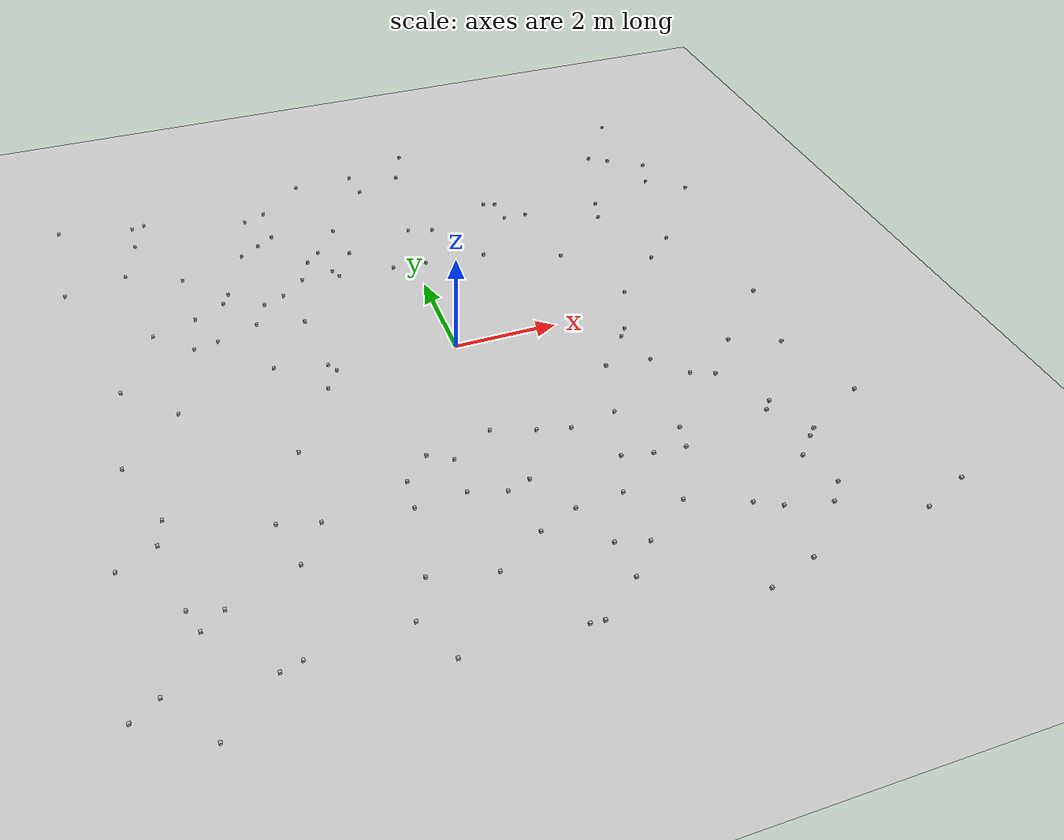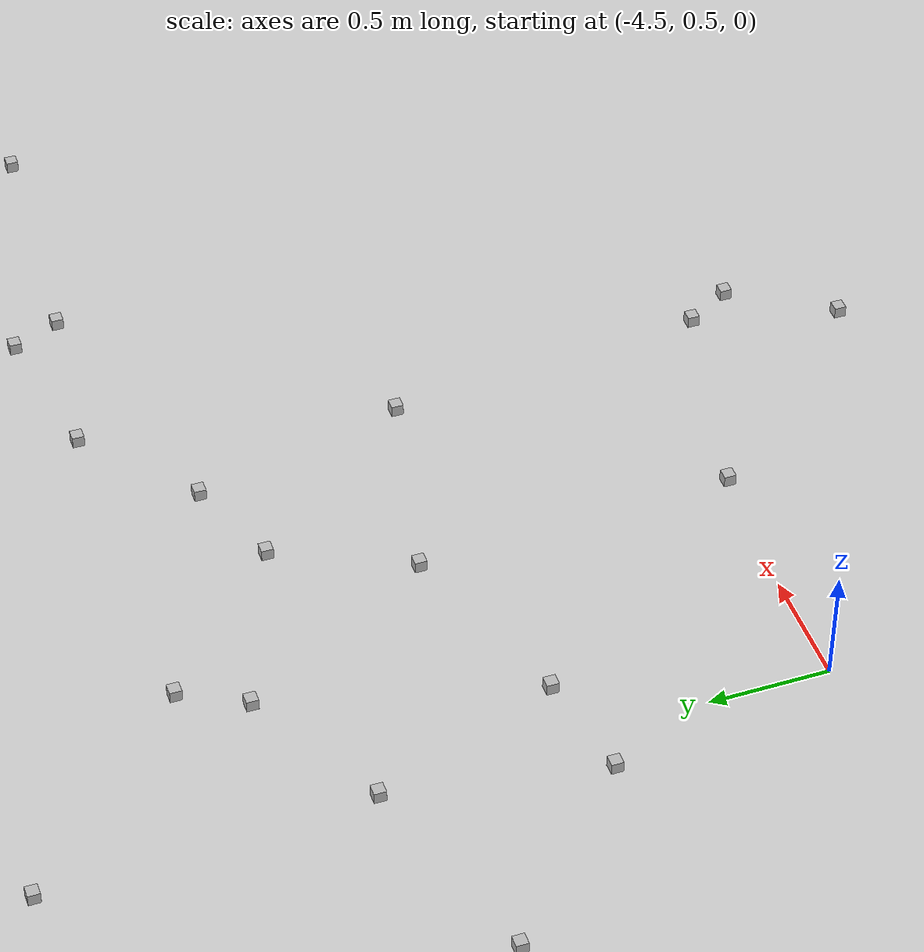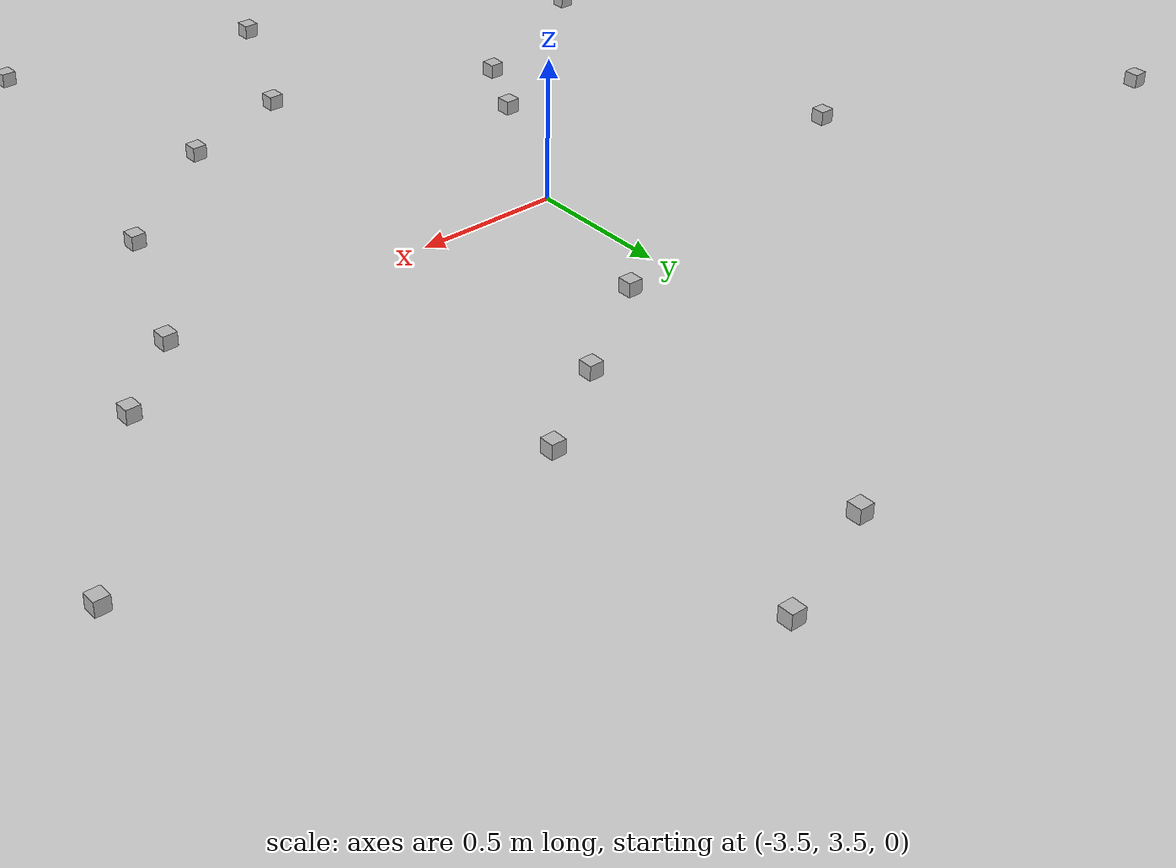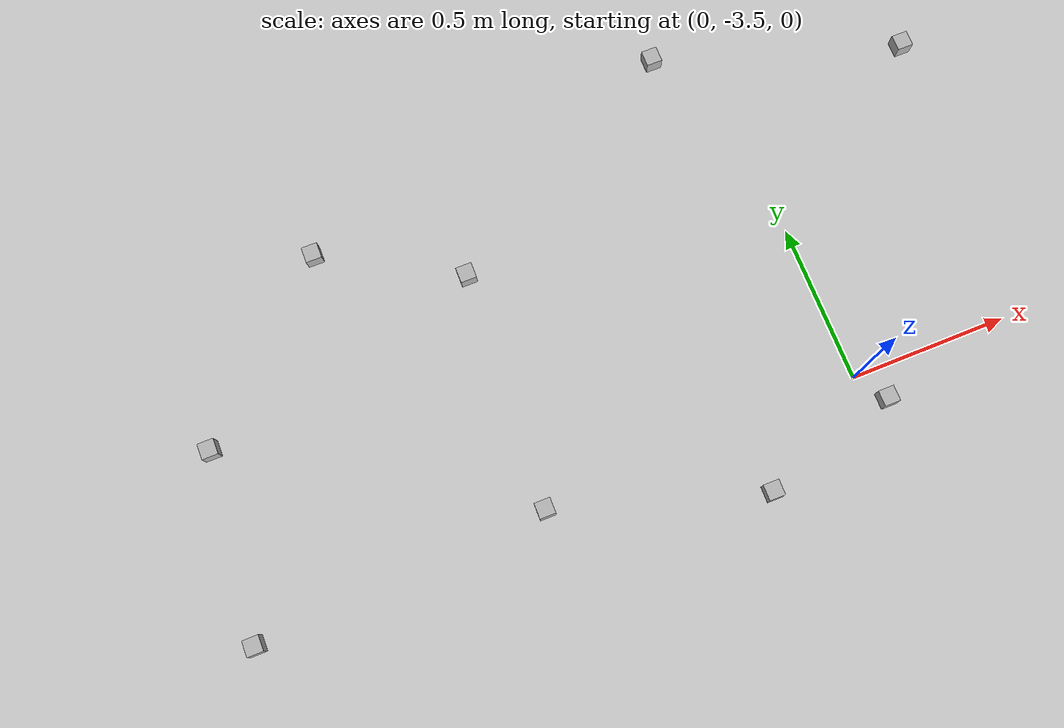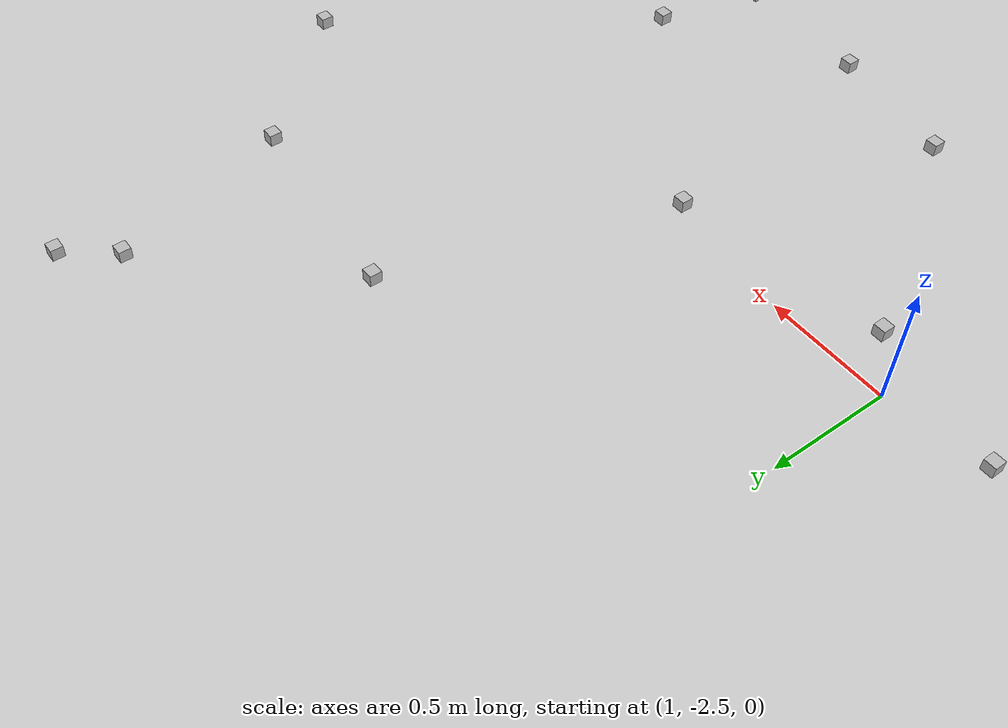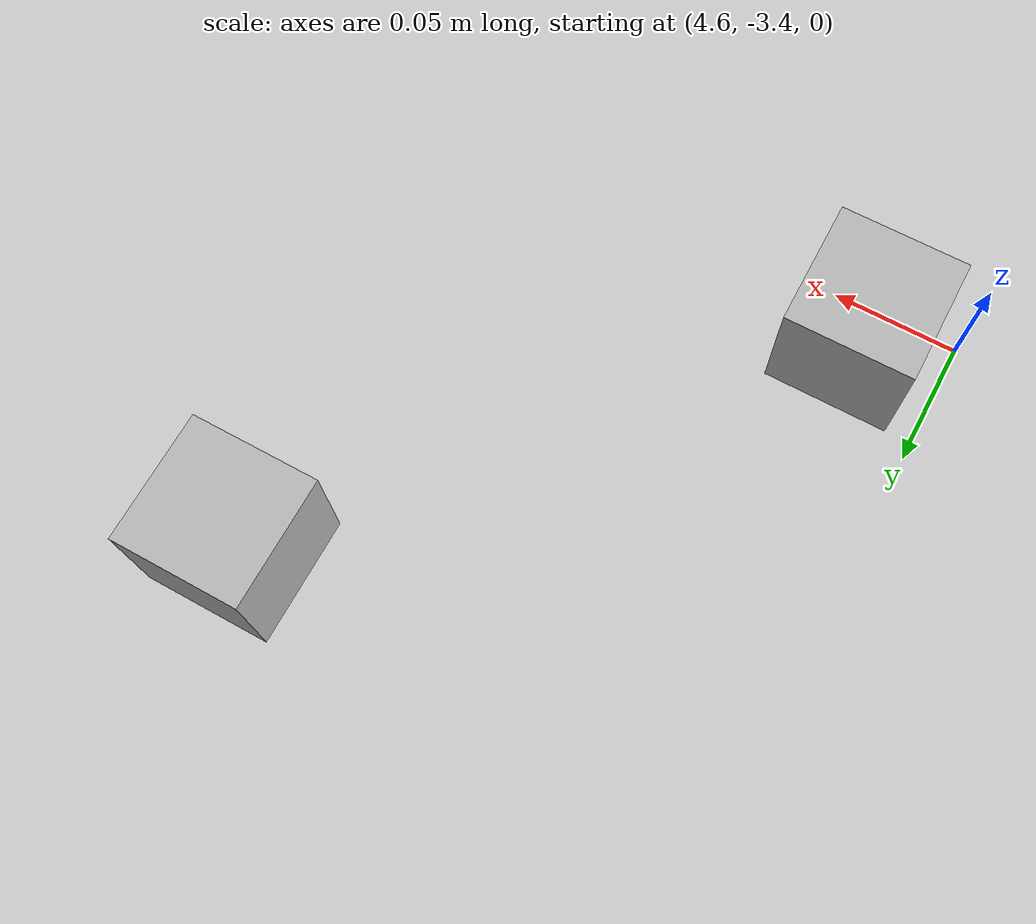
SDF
<sdf version="1.4">
 <world name="default">
  <model name="ground_plane">
   <static>1</static>
   <link name="link">
    <collision name="collision">
     <geometry><plane><normal>0 0 1</normal><size>100 100</size></plane></geometry>
     <surface><friction><ode><mu>100</mu><mu2>50</mu2></ode></friction></surface>
    </collision>
    <visual name="visual">
     <cast_shadows>0</cast_shadows>
     <geometry><plane><normal>0 0 1</normal><size>100 100</size></plane></geometry>
     <material>
      <script><uri>file://media/materials/scripts/gazebo.material</uri><name>Gazebo/Grey</name></script>
     </material>
    </visual>
    <velocity_decay><linear>0</linear><angular>0</angular></velocity_decay>
   </link>
  </model>
  <light name="sun" type="directional">
   <pose>0 0 10 0 -0 0</pose>
   <diffuse>0.8 0.8 0.8 1</diffuse>
   <specular>0.2 0.2 0.2 1</specular>
   <attenuation>
    <range>1000</range>
    <constant>0.9</constant>
    <linear>0.01</linear>
    <quadratic>0.001</quadratic>
   </attenuation>
   <direction>-0.5 0.1 -0.9</direction>
  </light>
  <plugin name="SetupWorld" filename="libgazebo_plugins.so"/>
  <physics type="ode">
   <max_step_size>0.001</max_step_size>
   <real_time_factor>1</real_time_factor>
   <real_time_update_rate>1000</real_time_update_rate>
   <gravity>0 0 -9.8</gravity>
  </physics>
  <scene><ambient>0.4 0.4 0.4 1</ambient><background>0.7 0.7 0.7 1</background><shadows>1</shadows></scene>
  <spherical_coordinates>
   <surface_model>EARTH_WGS84</surface_model>
   <latitude_deg>0</latitude_deg>
   <longitude_deg>0</longitude_deg>
   <elevation>0</elevation>
   <heading_deg>0</heading_deg>
  </spherical_coordinates>
  <model name="at0">
   <static>0</static>
   <link name="link">
    <inertial>
     <mass>0.01</mass>
     <inertia><ixx>4e-05</ixx><ixy>0</ixy><ixz>0</ixz><iyy>4e-05</iyy><iyz>0</iyz><izz>4e-05</izz></inertia>
    </inertial>
    <visual name="visual">
     <geometry><box><size>0.05 0.05 0.05</size></box></geometry>
     <material>
      <script>
       <uri>model://at0/materials/scripts</uri>
       <uri>model://at0/materials/textures</uri>
       <name>at0/Diffuse</name>
      </script>
     </material>
    </visual>
    <collision name="collision">
     <geometry><box><size>0.05 0.05 0.05</size></box></geometry>
     <surface><friction><ode><mu>0.8</mu><mu2>0.7</mu2></ode></friction></surface>
    </collision>
    <velocity_decay><linear>0</linear><angular>0</angular></velocity_decay>
   </link>
   <pose>-4.69459 1.45752 0.025 0 -0 0</pose>
  </model>
  <model name="at1">
   <static>0</static>
   <link name="link">
    <inertial>
     <mass>0.01</mass>
     <inertia><ixx>4e-05</ixx><ixy>0</ixy><ixz>0</ixz><iyy>4e-05</iyy><iyz>0</iyz><izz>4e-05</izz></inertia>
    </inertial>
    <visual name="visual">
     <geometry><box><size>0.05 0.05 0.05</size></box></geometry>
     <material>
      <script>
       <uri>model://at0/materials/scripts</uri>
       <uri>model://at0/materials/textures</uri>
       <name>at0/Diffuse</name>
      </script>
     </material>
    </visual>
    <collision name="collision">
     <geometry><box><size>0.05 0.05 0.05</size></box></geometry>
     <surface><friction><ode><mu>0.8</mu><mu2>0.7</mu2></ode></friction></surface>
    </collision>
    <velocity_decay><linear>0</linear><angular>0</angular></velocity_decay>
   </link>
   <pose>-3.90677 -4.11847 0.025 0 -0 0</pose>
  </model>
  <model name="at2">
   <static>0</static>
   <link name="link">
    <inertial>
     <mass>0.01</mass>
     <inertia><ixx>4e-05</ixx><ixy>0</ixy><ixz>0</ixz><iyy>4e-05</iyy><iyz>0</iyz><izz>4e-05</izz></inertia>
    </inertial>
    <visual name="visual">
     <geometry><box><size>0.05 0.05 0.05</size></box></geometry>
     <material>
      <script>
       <uri>model://at0/materials/scripts</uri>
       <uri>model://at0/materials/textures</uri>
       <name>at0/Diffuse</name>
      </script>
     </material>
    </visual>
    <collision name="collision">
     <geometry><box><size>0.05 0.05 0.05</size></box></geometry>
     <surface><friction><ode><mu>0.8</mu><mu2>0.7</mu2></ode></friction></surface>
    </collision>
    <velocity_decay><linear>0</linear><angular>0</angular></velocity_decay>
   </link>
   <pose>-5.68073 4.17379 0.025 0 -0 0</pose>
  </model>
  <model name="at3">
   <static>0</static>
   <link name="link">
    <inertial>
     <mass>0.01</mass>
     <inertia><ixx>4e-05</ixx><ixy>0</ixy><ixz>0</ixz><iyy>4e-05</iyy><iyz>0</iyz><izz>4e-05</izz></inertia>
    </inertial>
    <visual name="visual">
     <geometry><box><size>0.05 0.05 0.05</size></box></geometry>
     <material>
      <script>
       <uri>model://at0/materials/scripts</uri>
       <uri>model://at0/materials/textures</uri>
       <name>at0/Diffuse</name>
      </script>
     </material>
    </visual>
    <collision name="collision">
     <geometry><box><size>0.05 0.05 0.05</size></box></geometry>
     <surface><friction><ode><mu>0.8</mu><mu2>0.7</mu2></ode></friction></surface>
    </collision>
    <velocity_decay><linear>0</linear><angular>0</angular></velocity_decay>
   </link>
   <pose>2.27393 -3.70157 0.025 0 -0 0</pose>
  </model>
  <model name="at4">
   <static>0</static>
   <link name="link">
    <inertial>
     <mass>0.01</mass>
     <inertia><ixx>4e-05</ixx><ixy>0</ixy><ixz>0</ixz><iyy>4e-05</iyy><iyz>0</iyz><izz>4e-05</izz></inertia>
    </inertial>
    <visual name="visual">
     <geometry><box><size>0.05 0.05 0.05</size></box></geometry>
     <material>
      <script>
       <uri>model://at0/materials/scripts</uri>
       <uri>model://at0/materials/textures</uri>
       <name>at0/Diffuse</name>
      </script>
     </material>
    </visual>
    <collision name="collision">
     <geometry><box><size>0.05 0.05 0.05</size></box></geometry>
     <surface><friction><ode><mu>0.8</mu><mu2>0.7</mu2></ode></friction></surface>
    </collision>
    <velocity_decay><linear>0</linear><angular>0</angular></velocity_decay>
   </link>
   <pose>3.06671 -0.744786 0.025 0 -0 0</pose>
  </model>
  <model name="at5">
   <static>0</static>
   <link name="link">
    <inertial>
     <mass>0.01</mass>
     <inertia><ixx>4e-05</ixx><ixy>0</ixy><ixz>0</ixz><iyy>4e-05</iyy><iyz>0</iyz><izz>4e-05</izz></inertia>
    </inertial>
    <visual name="visual">
     <geometry><box><size>0.05 0.05 0.05</size></box></geometry>
     <material>
      <script>
       <uri>model://at0/materials/scripts</uri>
       <uri>model://at0/materials/textures</uri>
       <name>at0/Diffuse</name>
      </script>
     </material>
    </visual>
    <collision name="collision">
     <geometry><box><size>0.05 0.05 0.05</size></box></geometry>
     <surface><friction><ode><mu>0.8</mu><mu2>0.7</mu2></ode></friction></surface>
    </collision>
    <velocity_decay><linear>0</linear><angular>0</angular></velocity_decay>
   </link>
   <pose>-3.41245 -3.39957 0.025 0 -0 0</pose>
  </model>
  <model name="at6">
   <static>0</static>
   <link name="link">
    <inertial>
     <mass>0.01</mass>
     <inertia><ixx>4e-05</ixx><ixy>0</ixy><ixz>0</ixz><iyy>4e-05</iyy><iyz>0</iyz><izz>4e-05</izz></inertia>
    </inertial>
    <visual name="visual">
     <geometry><box><size>0.05 0.05 0.05</size></box></geometry>
     <material>
      <script>
       <uri>model://at0/materials/scripts</uri>
       <uri>model://at0/materials/textures</uri>
       <name>at0/Diffuse</name>
      </script>
     </material>
    </visual>
    <collision name="collision">
     <geometry><box><size>0.05 0.05 0.05</size></box></geometry>
     <surface><friction><ode><mu>0.8</mu><mu2>0.7</mu2></ode></friction></surface>
    </collision>
    <velocity_decay><linear>0</linear><angular>0</angular></velocity_decay>
   </link>
   <pose>3.71021 0.488781 0.025 0 -0 0</pose>
  </model>
  <model name="at7">
   <static>0</static>
   <link name="link">
    <inertial>
     <mass>0.01</mass>
     <inertia><ixx>4e-05</ixx><ixy>0</ixy><ixz>0</ixz><iyy>4e-05</iyy><iyz>0</iyz><izz>4e-05</izz></inertia>
    </inertial>
    <visual name="visual">
     <geometry><box><size>0.05 0.05 0.05</size></box></geometry>
     <material>
      <script>
       <uri>model://at0/materials/scripts</uri>
       <uri>model://at0/materials/textures</uri>
       <name>at0/Diffuse</name>
      </script>
     </material>
    </visual>
    <collision name="collision">
     <geometry><box><size>0.05 0.05 0.05</size></box></geometry>
     <surface><friction><ode><mu>0.8</mu><mu2>0.7</mu2></ode></friction></surface>
    </collision>
    <velocity_decay><linear>0</linear><angular>0</angular></velocity_decay>
   </link>
   <pose>-6.24077 -5.74349 0.025 0 -0 0</pose>
  </model>
  <model name="at8">
   <static>0</static>
   <link name="link">
    <inertial>
     <mass>0.01</mass>
     <inertia><ixx>4e-05</ixx><ixy>0</ixy><ixz>0</ixz><iyy>4e-05</iyy><iyz>0</iyz><izz>4e-05</izz></inertia>
    </inertial>
    <visual name="visual">
     <geometry><box><size>0.05 0.05 0.05</size></box></geometry>
     <material>
      <script>
       <uri>model://at0/materials/scripts</uri>
       <uri>model://at0/materials/textures</uri>
       <name>at0/Diffuse</name>
      </script>
     </material>
    </visual>
    <collision name="collision">
     <geometry><box><size>0.05 0.05 0.05</size></box></geometry>
     <surface><friction><ode><mu>0.8</mu><mu2>0.7</mu2></ode></friction></surface>
    </collision>
    <velocity_decay><linear>0</linear><angular>0</angular></velocity_decay>
   </link>
   <pose>-1.87282 -2.9987 0.025 0 -0 0</pose>
  </model>
  <model name="at9">
   <static>0</static>
   <link name="link">
    <inertial>
     <mass>0.01</mass>
     <inertia><ixx>4e-05</ixx><ixy>0</ixy><ixz>0</ixz><iyy>4e-05</iyy><iyz>0</iyz><izz>4e-05</izz></inertia>
    </inertial>
    <visual name="visual">
     <geometry><box><size>0.05 0.05 0.05</size></box></geometry>
     <material>
      <script>
       <uri>model://at0/materials/scripts</uri>
       <uri>model://at0/materials/textures</uri>
       <name>at0/Diffuse</name>
      </script>
     </material>
    </visual>
    <collision name="collision">
     <geometry><box><size>0.05 0.05 0.05</size></box></geometry>
     <surface><friction><ode><mu>0.8</mu><mu2>0.7</mu2></ode></friction></surface>
    </collision>
    <velocity_decay><linear>0</linear><angular>0</angular></velocity_decay>
   </link>
   <pose>4.94588 -1.47617 0.025 0 -0 0</pose>
  </model>
  <model name="at10">
   <static>0</static>
   <link name="link">
    <inertial>
     <mass>0.01</mass>
     <inertia><ixx>4e-05</ixx><ixy>0</ixy><ixz>0</ixz><iyy>4e-05</iyy><iyz>0</iyz><izz>4e-05</izz></inertia>
    </inertial>
    <visual name="visual">
     <geometry><box><size>0.05 0.05 0.05</size></box></geometry>
     <material>
      <script>
       <uri>model://at0/materials/scripts</uri>
       <uri>model://at0/materials/textures</uri>
       <name>at0/Diffuse</name>
      </script>
     </material>
    </visual>
    <collision name="collision">
     <geometry><box><size>0.05 0.05 0.05</size></box></geometry>
     <surface><friction><ode><mu>0.8</mu><mu2>0.7</mu2></ode></friction></surface>
    </collision>
    <velocity_decay><linear>0</linear><angular>0</angular></velocity_decay>
   </link>
   <pose>6.67505 3.54816 0.025 0 -0 0</pose>
  </model>
  <model name="at11">
   <static>0</static>
   <link name="link">
    <inertial>
     <mass>0.01</mass>
     <inertia><ixx>4e-05</ixx><ixy>0</ixy><ixz>0</ixz><iyy>4e-05</iyy><iyz>0</iyz><izz>4e-05</izz></inertia>
    </inertial>
    <visual name="visual">
     <geometry><box><size>0.05 0.05 0.05</size></box></geometry>
     <material>
      <script>
       <uri>model://at0/materials/scripts</uri>
       <uri>model://at0/materials/textures</uri>
       <name>at0/Diffuse</name>
      </script>
     </material>
    </visual>
    <collision name="collision">
     <geometry><box><size>0.05 0.05 0.05</size></box></geometry>
     <surface><friction><ode><mu>0.8</mu><mu2>0.7</mu2></ode></friction></surface>
    </collision>
    <velocity_decay><linear>0</linear><angular>0</angular></velocity_decay>
   </link>
   <pose>5.0062 -4.19764 0.025 0 -0 0</pose>
  </model>
  <model name="at12">
   <static>0</static>
   <link name="link">
    <inertial>
     <mass>0.01</mass>
     <inertia><ixx>4e-05</ixx><ixy>0</ixy><ixz>0</ixz><iyy>4e-05</iyy><iyz>0</iyz><izz>4e-05</izz></inertia>
    </inertial>
    <visual name="visual">
     <geometry><box><size>0.05 0.05 0.05</size></box></geometry>
     <material>
      <script>
       <uri>model://at0/materials/scripts</uri>
       <uri>model://at0/materials/textures</uri>
       <name>at0/Diffuse</name>
      </script>
     </material>
    </visual>
    <collision name="collision">
     <geometry><box><size>0.05 0.05 0.05</size></box></geometry>
     <surface><friction><ode><mu>0.8</mu><mu2>0.7</mu2></ode></friction></surface>
    </collision>
    <velocity_decay><linear>0</linear><angular>0</angular></velocity_decay>
   </link>
   <pose>4.73783 1.36697 0.025 0 -0 0</pose>
  </model>
  <model name="at13">
   <static>0</static>
   <link name="link">
    <inertial>
     <mass>0.01</mass>
     <inertia><ixx>4e-05</ixx><ixy>0</ixy><ixz>0</ixz><iyy>4e-05</iyy><iyz>0</iyz><izz>4e-05</izz></inertia>
    </inertial>
    <visual name="visual">
     <geometry><box><size>0.05 0.05 0.05</size></box></geometry>
     <material>
      <script>
       <uri>model://at0/materials/scripts</uri>
       <uri>model://at0/materials/textures</uri>
       <name>at0/Diffuse</name>
      </script>
     </material>
    </visual>
    <collision name="collision">
     <geometry><box><size>0.05 0.05 0.05</size></box></geometry>
     <surface><friction><ode><mu>0.8</mu><mu2>0.7</mu2></ode></friction></surface>
    </collision>
    <velocity_decay><linear>0</linear><angular>0</angular></velocity_decay>
   </link>
   <pose>5.10889 5.39844 0.025 0 -0 0</pose>
  </model>
  <model name="at14">
   <static>0</static>
   <link name="link">
    <inertial>
     <mass>0.01</mass>
     <inertia><ixx>4e-05</ixx><ixy>0</ixy><ixz>0</ixz><iyy>4e-05</iyy><iyz>0</iyz><izz>4e-05</izz></inertia>
    </inertial>
    <visual name="visual">
     <geometry><box><size>0.05 0.05 0.05</size></box></geometry>
     <material>
      <script>
       <uri>model://at0/materials/scripts</uri>
       <uri>model://at0/materials/textures</uri>
       <name>at0/Diffuse</name>
      </script>
     </material>
    </visual>
    <collision name="collision">
     <geometry><box><size>0.05 0.05 0.05</size></box></geometry>
     <surface><friction><ode><mu>0.8</mu><mu2>0.7</mu2></ode></friction></surface>
    </collision>
    <velocity_decay><linear>0</linear><angular>0</angular></velocity_decay>
   </link>
   <pose>-6.88516 3.88805 0.025 0 -0 0</pose>
  </model>
  <model name="at15">
   <static>0</static>
   <link name="link">
    <inertial>
     <mass>0.01</mass>
     <inertia><ixx>4e-05</ixx><ixy>0</ixy><ixz>0</ixz><iyy>4e-05</iyy><iyz>0</iyz><izz>4e-05</izz></inertia>
    </inertial>
    <visual name="visual">
     <geometry><box><size>0.05 0.05 0.05</size></box></geometry>
     <material>
      <script>
       <uri>model://at0/materials/scripts</uri>
       <uri>model://at0/materials/textures</uri>
       <name>at0/Diffuse</name>
      </script>
     </material>
    </visual>
    <collision name="collision">
     <geometry><box><size>0.05 0.05 0.05</size></box></geometry>
     <surface><friction><ode><mu>0.8</mu><mu2>0.7</mu2></ode></friction></surface>
    </collision>
    <velocity_decay><linear>0</linear><angular>0</angular></velocity_decay>
   </link>
   <pose>-0.178467 -4.67975 0.025 0 -0 0</pose>
  </model>
  <model name="at16">
   <static>0</static>
   <link name="link">
    <inertial>
     <mass>0.01</mass>
     <inertia><ixx>4e-05</ixx><ixy>0</ixy><ixz>0</ixz><iyy>4e-05</iyy><iyz>0</iyz><izz>4e-05</izz></inertia>
    </inertial>
    <visual name="visual">
     <geometry><box><size>0.05 0.05 0.05</size></box></geometry>
     <material>
      <script>
       <uri>model://at0/materials/scripts</uri>
       <uri>model://at0/materials/textures</uri>
       <name>at0/Diffuse</name>
      </script>
     </material>
    </visual>
    <collision name="collision">
     <geometry><box><size>0.05 0.05 0.05</size></box></geometry>
     <surface><friction><ode><mu>0.8</mu><mu2>0.7</mu2></ode></friction></surface>
    </collision>
    <velocity_decay><linear>0</linear><angular>0</angular></velocity_decay>
   </link>
   <pose>-1.55443 2.81476 0.025 0 -0 0</pose>
  </model>
  <model name="at17">
   <static>0</static>
   <link name="link">
    <inertial>
     <mass>0.01</mass>
     <inertia><ixx>4e-05</ixx><ixy>0</ixy><ixz>0</ixz><iyy>4e-05</iyy><iyz>0</iyz><izz>4e-05</izz></inertia>
    </inertial>
    <visual name="visual">
     <geometry><box><size>0.05 0.05 0.05</size></box></geometry>
     <material>
      <script>
       <uri>model://at0/materials/scripts</uri>
       <uri>model://at0/materials/textures</uri>
       <name>at0/Diffuse</name>
      </script>
     </material>
    </visual>
    <collision name="collision">
     <geometry><box><size>0.05 0.05 0.05</size></box></geometry>
     <surface><friction><ode><mu>0.8</mu><mu2>0.7</mu2></ode></friction></surface>
    </collision>
    <velocity_decay><linear>0</linear><angular>0</angular></velocity_decay>
   </link>
   <pose>-0.435567 2.74024 0.025 0 -0 0</pose>
  </model>
  <model name="at18">
   <static>0</static>
   <link name="link">
    <inertial>
     <mass>0.01</mass>
     <inertia><ixx>4e-05</ixx><ixy>0</ixy><ixz>0</ixz><iyy>4e-05</iyy><iyz>0</iyz><izz>4e-05</izz></inertia>
    </inertial>
    <visual name="visual">
     <geometry><box><size>0.05 0.05 0.05</size></box></geometry>
     <material>
      <script>
       <uri>model://at0/materials/scripts</uri>
       <uri>model://at0/materials/textures</uri>
       <name>at0/Diffuse</name>
      </script>
     </material>
    </visual>
    <collision name="collision">
     <geometry><box><size>0.05 0.05 0.05</size></box></geometry>
     <surface><friction><ode><mu>0.8</mu><mu2>0.7</mu2></ode></friction></surface>
    </collision>
    <velocity_decay><linear>0</linear><angular>0</angular></velocity_decay>
   </link>
   <pose>0.088555 -6.5243 0.025 0 -0 0</pose>
  </model>
  <model name="at19">
   <static>0</static>
   <link name="link">
    <inertial>
     <mass>0.01</mass>
     <inertia><ixx>4e-05</ixx><ixy>0</ixy><ixz>0</ixz><iyy>4e-05</iyy><iyz>0</iyz><izz>4e-05</izz></inertia>
    </inertial>
    <visual name="visual">
     <geometry><box><size>0.05 0.05 0.05</size></box></geometry>
     <material>
      <script>
       <uri>model://at0/materials/scripts</uri>
       <uri>model://at0/materials/textures</uri>
       <name>at0/Diffuse</name>
      </script>
     </material>
    </visual>
    <collision name="collision">
     <geometry><box><size>0.05 0.05 0.05</size></box></geometry>
     <surface><friction><ode><mu>0.8</mu><mu2>0.7</mu2></ode></friction></surface>
    </collision>
    <velocity_decay><linear>0</linear><angular>0</angular></velocity_decay>
   </link>
   <pose>2.86327 -3.74474 0.025 0 -0 0</pose>
  </model>
  <model name="at20">
   <static>0</static>
   <link name="link">
    <inertial>
     <mass>0.01</mass>
     <inertia><ixx>4e-05</ixx><ixy>0</ixy><ixz>0</ixz><iyy>4e-05</iyy><iyz>0</iyz><izz>4e-05</izz></inertia>
    </inertial>
    <visual name="visual">
     <geometry><box><size>0.05 0.05 0.05</size></box></geometry>
     <material>
      <script>
       <uri>model://at0/materials/scripts</uri>
       <uri>model://at0/materials/textures</uri>
       <name>at0/Diffuse</name>
      </script>
     </material>
    </visual>
    <collision name="collision">
     <geometry><box><size>0.05 0.05 0.05</size></box></geometry>
     <surface><friction><ode><mu>0.8</mu><mu2>0.7</mu2></ode></friction></surface>
    </collision>
    <velocity_decay><linear>0</linear><angular>0</angular></velocity_decay>
   </link>
   <pose>-0.369081 -3.72481 0.025 0 -0 0</pose>
  </model>
  <model name="at21">
   <static>0</static>
   <link name="link">
    <inertial>
     <mass>0.01</mass>
     <inertia><ixx>4e-05</ixx><ixy>0</ixy><ixz>0</ixz><iyy>4e-05</iyy><iyz>0</iyz><izz>4e-05</izz></inertia>
    </inertial>
    <visual name="visual">
     <geometry><box><size>0.05 0.05 0.05</size></box></geometry>
     <material>
      <script>
       <uri>model://at0/materials/scripts</uri>
       <uri>model://at0/materials/textures</uri>
       <name>at0/Diffuse</name>
      </script>
     </material>
    </visual>
    <collision name="collision">
     <geometry><box><size>0.05 0.05 0.05</size></box></geometry>
     <surface><friction><ode><mu>0.8</mu><mu2>0.7</mu2></ode></friction></surface>
    </collision>
    <velocity_decay><linear>0</linear><angular>0</angular></velocity_decay>
   </link>
   <pose>1.37684 -5.40311 0.025 0 -0 0</pose>
  </model>
  <model name="at22">
   <static>0</static>
   <link name="link">
    <inertial>
     <mass>0.01</mass>
     <inertia><ixx>4e-05</ixx><ixy>0</ixy><ixz>0</ixz><iyy>4e-05</iyy><iyz>0</iyz><izz>4e-05</izz></inertia>
    </inertial>
    <visual name="visual">
     <geometry><box><size>0.05 0.05 0.05</size></box></geometry>
     <material>
      <script>
       <uri>model://at0/materials/scripts</uri>
       <uri>model://at0/materials/textures</uri>
       <name>at0/Diffuse</name>
      </script>
     </material>
    </visual>
    <collision name="collision">
     <geometry><box><size>0.05 0.05 0.05</size></box></geometry>
     <surface><friction><ode><mu>0.8</mu><mu2>0.7</mu2></ode></friction></surface>
    </collision>
    <velocity_decay><linear>0</linear><angular>0</angular></velocity_decay>
   </link>
   <pose>2.99026 2.03607 0.025 0 -0 0</pose>
  </model>
  <model name="at23">
   <static>0</static>
   <link name="link">
    <inertial>
     <mass>0.01</mass>
     <inertia><ixx>4e-05</ixx><ixy>0</ixy><ixz>0</ixz><iyy>4e-05</iyy><iyz>0</iyz><izz>4e-05</izz></inertia>
    </inertial>
    <visual name="visual">
     <geometry><box><size>0.05 0.05 0.05</size></box></geometry>
     <material>
      <script>
       <uri>model://at0/materials/scripts</uri>
       <uri>model://at0/materials/textures</uri>
       <name>at0/Diffuse</name>
      </script>
     </material>
    </visual>
    <collision name="collision">
     <geometry><box><size>0.05 0.05 0.05</size></box></geometry>
     <surface><friction><ode><mu>0.8</mu><mu2>0.7</mu2></ode></friction></surface>
    </collision>
    <velocity_decay><linear>0</linear><angular>0</angular></velocity_decay>
   </link>
   <pose>-4.2466 -5.78257 0.025 0 -0 0</pose>
  </model>
  <model name="at24">
   <static>0</static>
   <link name="link">
    <inertial>
     <mass>0.01</mass>
     <inertia><ixx>4e-05</ixx><ixy>0</ixy><ixz>0</ixz><iyy>4e-05</iyy><iyz>0</iyz><izz>4e-05</izz></inertia>
    </inertial>
    <visual name="visual">
     <geometry><box><size>0.05 0.05 0.05</size></box></geometry>
     <material>
      <script>
       <uri>model://at0/materials/scripts</uri>
       <uri>model://at0/materials/textures</uri>
       <name>at0/Diffuse</name>
      </script>
     </material>
    </visual>
    <collision name="collision">
     <geometry><box><size>0.05 0.05 0.05</size></box></geometry>
     <surface><friction><ode><mu>0.8</mu><mu2>0.7</mu2></ode></friction></surface>
    </collision>
    <velocity_decay><linear>0</linear><angular>0</angular></velocity_decay>
   </link>
   <pose>5.93738 -6.20071 0.025 0 -0 0</pose>
  </model>
  <model name="at25">
   <static>0</static>
   <link name="link">
    <inertial>
     <mass>0.01</mass>
     <inertia><ixx>4e-05</ixx><ixy>0</ixy><ixz>0</ixz><iyy>4e-05</iyy><iyz>0</iyz><izz>4e-05</izz></inertia>
    </inertial>
    <visual name="visual">
     <geometry><box><size>0.05 0.05 0.05</size></box></geometry>
     <material>
      <script>
       <uri>model://at0/materials/scripts</uri>
       <uri>model://at0/materials/textures</uri>
       <name>at0/Diffuse</name>
      </script>
     </material>
    </visual>
    <collision name="collision">
     <geometry><box><size>0.05 0.05 0.05</size></box></geometry>
     <surface><friction><ode><mu>0.8</mu><mu2>0.7</mu2></ode></friction></surface>
    </collision>
    <velocity_decay><linear>0</linear><angular>0</angular></velocity_decay>
   </link>
   <pose>-0.358736 5.71243 0.025 0 -0 0</pose>
  </model>
  <model name="at26">
   <static>0</static>
   <link name="link">
    <inertial>
     <mass>0.01</mass>
     <inertia><ixx>4e-05</ixx><ixy>0</ixy><ixz>0</ixz><iyy>4e-05</iyy><iyz>0</iyz><izz>4e-05</izz></inertia>
    </inertial>
    <visual name="visual">
     <geometry><box><size>0.05 0.05 0.05</size></box></geometry>
     <material>
      <script>
       <uri>model://at0/materials/scripts</uri>
       <uri>model://at0/materials/textures</uri>
       <name>at0/Diffuse</name>
      </script>
     </material>
    </visual>
    <collision name="collision">
     <geometry><box><size>0.05 0.05 0.05</size></box></geometry>
     <surface><friction><ode><mu>0.8</mu><mu2>0.7</mu2></ode></friction></surface>
    </collision>
    <velocity_decay><linear>0</linear><angular>0</angular></velocity_decay>
   </link>
   <pose>4.24745 -2.25253 0.025 0 -0 0</pose>
  </model>
  <model name="at27">
   <static>0</static>
   <link name="link">
    <inertial>
     <mass>0.01</mass>
     <inertia><ixx>4e-05</ixx><ixy>0</ixy><ixz>0</ixz><iyy>4e-05</iyy><iyz>0</iyz><izz>4e-05</izz></inertia>
    </inertial>
    <visual name="visual">
     <geometry><box><size>0.05 0.05 0.05</size></box></geometry>
     <material>
      <script>
       <uri>model://at0/materials/scripts</uri>
       <uri>model://at0/materials/textures</uri>
       <name>at0/Diffuse</name>
      </script>
     </material>
    </visual>
    <collision name="collision">
     <geometry><box><size>0.05 0.05 0.05</size></box></geometry>
     <surface><friction><ode><mu>0.8</mu><mu2>0.7</mu2></ode></friction></surface>
    </collision>
    <velocity_decay><linear>0</linear><angular>0</angular></velocity_decay>
   </link>
   <pose>-5.38521 2.08528 0.025 0 -0 0</pose>
  </model>
  <model name="at28">
   <static>0</static>
   <link name="link">
    <inertial>
     <mass>0.01</mass>
     <inertia><ixx>4e-05</ixx><ixy>0</ixy><ixz>0</ixz><iyy>4e-05</iyy><iyz>0</iyz><izz>4e-05</izz></inertia>
    </inertial>
    <visual name="visual">
     <geometry><box><size>0.05 0.05 0.05</size></box></geometry>
     <material>
      <script>
       <uri>model://at0/materials/scripts</uri>
       <uri>model://at0/materials/textures</uri>
       <name>at0/Diffuse</name>
      </script>
     </material>
    </visual>
    <collision name="collision">
     <geometry><box><size>0.05 0.05 0.05</size></box></geometry>
     <surface><friction><ode><mu>0.8</mu><mu2>0.7</mu2></ode></friction></surface>
    </collision>
    <velocity_decay><linear>0</linear><angular>0</angular></velocity_decay>
   </link>
   <pose>6.01444 6.62368 0.025 0 -0 0</pose>
  </model>
  <model name="at29">
   <static>0</static>
   <link name="link">
    <inertial>
     <mass>0.01</mass>
     <inertia><ixx>4e-05</ixx><ixy>0</ixy><ixz>0</ixz><iyy>4e-05</iyy><iyz>0</iyz><izz>4e-05</izz></inertia>
    </inertial>
    <visual name="visual">
     <geometry><box><size>0.05 0.05 0.05</size></box></geometry>
     <material>
      <script>
       <uri>model://at0/materials/scripts</uri>
       <uri>model://at0/materials/textures</uri>
       <name>at0/Diffuse</name>
      </script>
     </material>
    </visual>
    <collision name="collision">
     <geometry><box><size>0.05 0.05 0.05</size></box></geometry>
     <surface><friction><ode><mu>0.8</mu><mu2>0.7</mu2></ode></friction></surface>
    </collision>
    <velocity_decay><linear>0</linear><angular>0</angular></velocity_decay>
   </link>
   <pose>0.583716 6.02928 0.025 0 -0 0</pose>
  </model>
  <model name="at30">
   <static>0</static>
   <link name="link">
    <inertial>
     <mass>0.01</mass>
     <inertia><ixx>4e-05</ixx><ixy>0</ixy><ixz>0</ixz><iyy>4e-05</iyy><iyz>0</iyz><izz>4e-05</izz></inertia>
    </inertial>
    <visual name="visual">
     <geometry><box><size>0.05 0.05 0.05</size></box></geometry>
     <material>
      <script>
       <uri>model://at0/materials/scripts</uri>
       <uri>model://at0/materials/textures</uri>
       <name>at0/Diffuse</name>
      </script>
     </material>
    </visual>
    <collision name="collision">
     <geometry><box><size>0.05 0.05 0.05</size></box></geometry>
     <surface><friction><ode><mu>0.8</mu><mu2>0.7</mu2></ode></friction></surface>
    </collision>
    <velocity_decay><linear>0</linear><angular>0</angular></velocity_decay>
   </link>
   <pose>3.61174 -6.49475 0.025 0 -0 0</pose>
  </model>
  <model name="at31">
   <static>0</static>
   <link name="link">
    <inertial>
     <mass>0.01</mass>
     <inertia><ixx>4e-05</ixx><ixy>0</ixy><ixz>0</ixz><iyy>4e-05</iyy><iyz>0</iyz><izz>4e-05</izz></inertia>
    </inertial>
    <visual name="visual">
     <geometry><box><size>0.05 0.05 0.05</size></box></geometry>
     <material>
      <script>
       <uri>model://at0/materials/scripts</uri>
       <uri>model://at0/materials/textures</uri>
       <name>at0/Diffuse</name>
      </script>
     </material>
    </visual>
    <collision name="collision">
     <geometry><box><size>0.05 0.05 0.05</size></box></geometry>
     <surface><friction><ode><mu>0.8</mu><mu2>0.7</mu2></ode></friction></surface>
    </collision>
    <velocity_decay><linear>0</linear><angular>0</angular></velocity_decay>
   </link>
   <pose>-5.55047 -4.84269 0.025 0 -0 0</pose>
  </model>
  <model name="at32">
   <static>0</static>
   <link name="link">
    <inertial>
     <mass>0.01</mass>
     <inertia><ixx>4e-05</ixx><ixy>0</ixy><ixz>0</ixz><iyy>4e-05</iyy><iyz>0</iyz><izz>4e-05</izz></inertia>
    </inertial>
    <visual name="visual">
     <geometry><box><size>0.05 0.05 0.05</size></box></geometry>
     <material>
      <script>
       <uri>model://at0/materials/scripts</uri>
       <uri>model://at0/materials/textures</uri>
       <name>at0/Diffuse</name>
      </script>
     </material>
    </visual>
    <collision name="collision">
     <geometry><box><size>0.05 0.05 0.05</size></box></geometry>
     <surface><friction><ode><mu>0.8</mu><mu2>0.7</mu2></ode></friction></surface>
    </collision>
    <velocity_decay><linear>0</linear><angular>0</angular></velocity_decay>
   </link>
   <pose>3.22001 -0.548693 0.025 0 -0 0</pose>
  </model>
  <model name="at33">
   <static>0</static>
   <link name="link">
    <inertial>
     <mass>0.01</mass>
     <inertia><ixx>4e-05</ixx><ixy>0</ixy><ixz>0</ixz><iyy>4e-05</iyy><iyz>0</iyz><izz>4e-05</izz></inertia>
    </inertial>
    <visual name="visual">
     <geometry><box><size>0.05 0.05 0.05</size></box></geometry>
     <material>
      <script>
       <uri>model://at0/materials/scripts</uri>
       <uri>model://at0/materials/textures</uri>
       <name>at0/Diffuse</name>
      </script>
     </material>
    </visual>
    <collision name="collision">
     <geometry><box><size>0.05 0.05 0.05</size></box></geometry>
     <surface><friction><ode><mu>0.8</mu><mu2>0.7</mu2></ode></friction></surface>
    </collision>
    <velocity_decay><linear>0</linear><angular>0</angular></velocity_decay>
   </link>
   <pose>1.72214 -3.59143 0.025 0 -0 0</pose>
  </model>
  <model name="at34">
   <static>0</static>
   <link name="link">
    <inertial>
     <mass>0.01</mass>
     <inertia><ixx>4e-05</ixx><ixy>0</ixy><ixz>0</ixz><iyy>4e-05</iyy><iyz>0</iyz><izz>4e-05</izz></inertia>
    </inertial>
    <visual name="visual">
     <geometry><box><size>0.05 0.05 0.05</size></box></geometry>
     <material>
      <script>
       <uri>model://at0/materials/scripts</uri>
       <uri>model://at0/materials/textures</uri>
       <name>at0/Diffuse</name>
      </script>
     </material>
    </visual>
    <collision name="collision">
     <geometry><box><size>0.05 0.05 0.05</size></box></geometry>
     <surface><friction><ode><mu>0.8</mu><mu2>0.7</mu2></ode></friction></surface>
    </collision>
    <velocity_decay><linear>0</linear><angular>0</angular></velocity_decay>
   </link>
   <pose>-0.172988 -2.31459 0.025 0 -0 0</pose>
  </model>
  <model name="at35">
   <static>0</static>
   <link name="link">
    <inertial>
     <mass>0.01</mass>
     <inertia><ixx>4e-05</ixx><ixy>0</ixy><ixz>0</ixz><iyy>4e-05</iyy><iyz>0</iyz><izz>4e-05</izz></inertia>
    </inertial>
    <visual name="visual">
     <geometry><box><size>0.05 0.05 0.05</size></box></geometry>
     <material>
      <script>
       <uri>model://at0/materials/scripts</uri>
       <uri>model://at0/materials/textures</uri>
       <name>at0/Diffuse</name>
      </script>
     </material>
    </visual>
    <collision name="collision">
     <geometry><box><size>0.05 0.05 0.05</size></box></geometry>
     <surface><friction><ode><mu>0.8</mu><mu2>0.7</mu2></ode></friction></surface>
    </collision>
    <velocity_decay><linear>0</linear><angular>0</angular></velocity_decay>
   </link>
   <pose>-0.436169 6.35793 0.025 0 -0 0</pose>
  </model>
  <model name="at36">
   <static>0</static>
   <link name="link">
    <inertial>
     <mass>0.01</mass>
     <inertia><ixx>4e-05</ixx><ixy>0</ixy><ixz>0</ixz><iyy>4e-05</iyy><iyz>0</iyz><izz>4e-05</izz></inertia>
    </inertial>
    <visual name="visual">
     <geometry><box><size>0.05 0.05 0.05</size></box></geometry>
     <material>
      <script>
       <uri>model://at0/materials/scripts</uri>
       <uri>model://at0/materials/textures</uri>
       <name>at0/Diffuse</name>
      </script>
     </material>
    </visual>
    <collision name="collision">
     <geometry><box><size>0.05 0.05 0.05</size></box></geometry>
     <surface><friction><ode><mu>0.8</mu><mu2>0.7</mu2></ode></friction></surface>
    </collision>
    <velocity_decay><linear>0</linear><angular>0</angular></velocity_decay>
   </link>
   <pose>0.860601 -5.95932 0.025 0 -0 0</pose>
  </model>
  <model name="at37">
   <static>0</static>
   <link name="link">
    <inertial>
     <mass>0.01</mass>
     <inertia><ixx>4e-05</ixx><ixy>0</ixy><ixz>0</ixz><iyy>4e-05</iyy><iyz>0</iyz><izz>4e-05</izz></inertia>
    </inertial>
    <visual name="visual">
     <geometry><box><size>0.05 0.05 0.05</size></box></geometry>
     <material>
      <script>
       <uri>model://at0/materials/scripts</uri>
       <uri>model://at0/materials/textures</uri>
       <name>at0/Diffuse</name>
      </script>
     </material>
    </visual>
    <collision name="collision">
     <geometry><box><size>0.05 0.05 0.05</size></box></geometry>
     <surface><friction><ode><mu>0.8</mu><mu2>0.7</mu2></ode></friction></surface>
    </collision>
    <velocity_decay><linear>0</linear><angular>0</angular></velocity_decay>
   </link>
   <pose>-5.94518 -3.04914 0.025 0 -0 0</pose>
  </model>
  <model name="at38">
   <static>0</static>
   <link name="link">
    <inertial>
     <mass>0.01</mass>
     <inertia><ixx>4e-05</ixx><ixy>0</ixy><ixz>0</ixz><iyy>4e-05</iyy><iyz>0</iyz><izz>4e-05</izz></inertia>
    </inertial>
    <visual name="visual">
     <geometry><box><size>0.05 0.05 0.05</size></box></geometry>
     <material>
      <script>
       <uri>model://at0/materials/scripts</uri>
       <uri>model://at0/materials/textures</uri>
       <name>at0/Diffuse</name>
      </script>
     </material>
    </visual>
    <collision name="collision">
     <geometry><box><size>0.05 0.05 0.05</size></box></geometry>
     <surface><friction><ode><mu>0.8</mu><mu2>0.7</mu2></ode></friction></surface>
    </collision>
    <velocity_decay><linear>0</linear><angular>0</angular></velocity_decay>
   </link>
   <pose>2.97675 -3.29177 0.025 0 -0 0</pose>
  </model>
  <model name="at39">
   <static>0</static>
   <link name="link">
    <inertial>
     <mass>0.01</mass>
     <inertia><ixx>4e-05</ixx><ixy>0</ixy><ixz>0</ixz><iyy>4e-05</iyy><iyz>0</iyz><izz>4e-05</izz></inertia>
    </inertial>
    <visual name="visual">
     <geometry><box><size>0.05 0.05 0.05</size></box></geometry>
     <material>
      <script>
       <uri>model://at0/materials/scripts</uri>
       <uri>model://at0/materials/textures</uri>
       <name>at0/Diffuse</name>
      </script>
     </material>
    </visual>
    <collision name="collision">
     <geometry><box><size>0.05 0.05 0.05</size></box></geometry>
     <surface><friction><ode><mu>0.8</mu><mu2>0.7</mu2></ode></friction></surface>
    </collision>
    <velocity_decay><linear>0</linear><angular>0</angular></velocity_decay>
   </link>
   <pose>1.4708 2.57775 0.025 0 -0 0</pose>
  </model>
  <model name="at40">
   <static>0</static>
   <link name="link">
    <inertial>
     <mass>0.01</mass>
     <inertia><ixx>4e-05</ixx><ixy>0</ixy><ixz>0</ixz><iyy>4e-05</iyy><iyz>0</iyz><izz>4e-05</izz></inertia>
    </inertial>
    <visual name="visual">
     <geometry><box><size>0.05 0.05 0.05</size></box></geometry>
     <material>
      <script>
       <uri>model://at0/materials/scripts</uri>
       <uri>model://at0/materials/textures</uri>
       <name>at0/Diffuse</name>
      </script>
     </material>
    </visual>
    <collision name="collision">
     <geometry><box><size>0.05 0.05 0.05</size></box></geometry>
     <surface><friction><ode><mu>0.8</mu><mu2>0.7</mu2></ode></friction></surface>
    </collision>
    <velocity_decay><linear>0</linear><angular>0</angular></velocity_decay>
   </link>
   <pose>-2.59249 4.60956 0.025 0 -0 0</pose>
  </model>
  <model name="at41">
   <static>0</static>
   <link name="link">
    <inertial>
     <mass>0.01</mass>
     <inertia><ixx>4e-05</ixx><ixy>0</ixy><ixz>0</ixz><iyy>4e-05</iyy><iyz>0</iyz><izz>4e-05</izz></inertia>
    </inertial>
    <visual name="visual">
     <geometry><box><size>0.05 0.05 0.05</size></box></geometry>
     <material>
      <script>
       <uri>model://at0/materials/scripts</uri>
       <uri>model://at0/materials/textures</uri>
       <name>at0/Diffuse</name>
      </script>
     </material>
    </visual>
    <collision name="collision">
     <geometry><box><size>0.05 0.05 0.05</size></box></geometry>
     <surface><friction><ode><mu>0.8</mu><mu2>0.7</mu2></ode></friction></surface>
    </collision>
    <velocity_decay><linear>0</linear><angular>0</angular></velocity_decay>
   </link>
   <pose>0.826558 -5.24504 0.025 0 -0 0</pose>
  </model>
  <model name="at42">
   <static>0</static>
   <link name="link">
    <inertial>
     <mass>0.01</mass>
     <inertia><ixx>4e-05</ixx><ixy>0</ixy><ixz>0</ixz><iyy>4e-05</iyy><iyz>0</iyz><izz>4e-05</izz></inertia>
    </inertial>
    <visual name="visual">
     <geometry><box><size>0.05 0.05 0.05</size></box></geometry>
     <material>
      <script>
       <uri>model://at0/materials/scripts</uri>
       <uri>model://at0/materials/textures</uri>
       <name>at0/Diffuse</name>
      </script>
     </material>
    </visual>
    <collision name="collision">
     <geometry><box><size>0.05 0.05 0.05</size></box></geometry>
     <surface><friction><ode><mu>0.8</mu><mu2>0.7</mu2></ode></friction></surface>
    </collision>
    <velocity_decay><linear>0</linear><angular>0</angular></velocity_decay>
   </link>
   <pose>-4.54297 2.34135 0.025 0 -0 0</pose>
  </model>
  <model name="at43">
   <static>0</static>
   <link name="link">
    <inertial>
     <mass>0.01</mass>
     <inertia><ixx>4e-05</ixx><ixy>0</ixy><ixz>0</ixz><iyy>4e-05</iyy><iyz>0</iyz><izz>4e-05</izz></inertia>
    </inertial>
    <visual name="visual">
     <geometry><box><size>0.05 0.05 0.05</size></box></geometry>
     <material>
      <script>
       <uri>model://at0/materials/scripts</uri>
       <uri>model://at0/materials/textures</uri>
       <name>at0/Diffuse</name>
      </script>
     </material>
    </visual>
    <collision name="collision">
     <geometry><box><size>0.05 0.05 0.05</size></box></geometry>
     <surface><friction><ode><mu>0.8</mu><mu2>0.7</mu2></ode></friction></surface>
    </collision>
    <velocity_decay><linear>0</linear><angular>0</angular></velocity_decay>
   </link>
   <pose>3.74024 -5.42854 0.025 0 -0 0</pose>
  </model>
  <model name="at44">
   <static>0</static>
   <link name="link">
    <inertial>
     <mass>0.01</mass>
     <inertia><ixx>4e-05</ixx><ixy>0</ixy><ixz>0</ixz><iyy>4e-05</iyy><iyz>0</iyz><izz>4e-05</izz></inertia>
    </inertial>
    <visual name="visual">
     <geometry><box><size>0.05 0.05 0.05</size></box></geometry>
     <material>
      <script>
       <uri>model://at0/materials/scripts</uri>
       <uri>model://at0/materials/textures</uri>
       <name>at0/Diffuse</name>
      </script>
     </material>
    </visual>
    <collision name="collision">
     <geometry><box><size>0.05 0.05 0.05</size></box></geometry>
     <surface><friction><ode><mu>0.8</mu><mu2>0.7</mu2></ode></friction></surface>
    </collision>
    <velocity_decay><linear>0</linear><angular>0</angular></velocity_decay>
   </link>
   <pose>2.06503 -2.57604 0.025 0 -0 0</pose>
  </model>
  <model name="at45">
   <static>0</static>
   <link name="link">
    <inertial>
     <mass>0.01</mass>
     <inertia><ixx>4e-05</ixx><ixy>0</ixy><ixz>0</ixz><iyy>4e-05</iyy><iyz>0</iyz><izz>4e-05</izz></inertia>
    </inertial>
    <visual name="visual">
     <geometry><box><size>0.05 0.05 0.05</size></box></geometry>
     <material>
      <script>
       <uri>model://at0/materials/scripts</uri>
       <uri>model://at0/materials/textures</uri>
       <name>at0/Diffuse</name>
      </script>
     </material>
    </visual>
    <collision name="collision">
     <geometry><box><size>0.05 0.05 0.05</size></box></geometry>
     <surface><friction><ode><mu>0.8</mu><mu2>0.7</mu2></ode></friction></surface>
    </collision>
    <velocity_decay><linear>0</linear><angular>0</angular></velocity_decay>
   </link>
   <pose>-6.29926 -1.22323 0.025 0 -0 0</pose>
  </model>
  <model name="at46">
   <static>0</static>
   <link name="link">
    <inertial>
     <mass>0.01</mass>
     <inertia><ixx>4e-05</ixx><ixy>0</ixy><ixz>0</ixz><iyy>4e-05</iyy><iyz>0</iyz><izz>4e-05</izz></inertia>
    </inertial>
    <visual name="visual">
     <geometry><box><size>0.05 0.05 0.05</size></box></geometry>
     <material>
      <script>
       <uri>model://at0/materials/scripts</uri>
       <uri>model://at0/materials/textures</uri>
       <name>at0/Diffuse</name>
      </script>
     </material>
    </visual>
    <collision name="collision">
     <geometry><box><size>0.05 0.05 0.05</size></box></geometry>
     <surface><friction><ode><mu>0.8</mu><mu2>0.7</mu2></ode></friction></surface>
    </collision>
    <velocity_decay><linear>0</linear><angular>0</angular></velocity_decay>
   </link>
   <pose>-2.1708 -4.94973 0.025 0 -0 0</pose>
  </model>
  <model name="at47">
   <static>0</static>
   <link name="link">
    <inertial>
     <mass>0.01</mass>
     <inertia><ixx>4e-05</ixx><ixy>0</ixy><ixz>0</ixz><iyy>4e-05</iyy><iyz>0</iyz><izz>4e-05</izz></inertia>
    </inertial>
    <visual name="visual">
     <geometry><box><size>0.05 0.05 0.05</size></box></geometry>
     <material>
      <script>
       <uri>model://at0/materials/scripts</uri>
       <uri>model://at0/materials/textures</uri>
       <name>at0/Diffuse</name>
      </script>
     </material>
    </visual>
    <collision name="collision">
     <geometry><box><size>0.05 0.05 0.05</size></box></geometry>
     <surface><friction><ode><mu>0.8</mu><mu2>0.7</mu2></ode></friction></surface>
    </collision>
    <velocity_decay><linear>0</linear><angular>0</angular></velocity_decay>
   </link>
   <pose>1.40157 -4.34378 0.025 0 -0 0</pose>
  </model>
  <model name="at48">
   <static>0</static>
   <link name="link">
    <inertial>
     <mass>0.01</mass>
     <inertia><ixx>4e-05</ixx><ixy>0</ixy><ixz>0</ixz><iyy>4e-05</iyy><iyz>0</iyz><izz>4e-05</izz></inertia>
    </inertial>
    <visual name="visual">
     <geometry><box><size>0.05 0.05 0.05</size></box></geometry>
     <material>
      <script>
       <uri>model://at0/materials/scripts</uri>
       <uri>model://at0/materials/textures</uri>
       <name>at0/Diffuse</name>
      </script>
     </material>
    </visual>
    <collision name="collision">
     <geometry><box><size>0.05 0.05 0.05</size></box></geometry>
     <surface><friction><ode><mu>0.8</mu><mu2>0.7</mu2></ode></friction></surface>
    </collision>
    <velocity_decay><linear>0</linear><angular>0</angular></velocity_decay>
   </link>
   <pose>-2.54222 -5.67141 0.025 0 -0 0</pose>
  </model>
  <model name="at49">
   <static>0</static>
   <link name="link">
    <inertial>
     <mass>0.01</mass>
     <inertia><ixx>4e-05</ixx><ixy>0</ixy><ixz>0</ixz><iyy>4e-05</iyy><iyz>0</iyz><izz>4e-05</izz></inertia>
    </inertial>
    <visual name="visual">
     <geometry><box><size>0.05 0.05 0.05</size></box></geometry>
     <material>
      <script>
       <uri>model://at0/materials/scripts</uri>
       <uri>model://at0/materials/textures</uri>
       <name>at0/Diffuse</name>
      </script>
     </material>
    </visual>
    <collision name="collision">
     <geometry><box><size>0.05 0.05 0.05</size></box></geometry>
     <surface><friction><ode><mu>0.8</mu><mu2>0.7</mu2></ode></friction></surface>
    </collision>
    <velocity_decay><linear>0</linear><angular>0</angular></velocity_decay>
   </link>
   <pose>0.241629 3.92162 0.025 0 -0 0</pose>
  </model>
  <model name="at50">
   <static>0</static>
   <link name="link">
    <inertial>
     <mass>0.01</mass>
     <inertia><ixx>4e-05</ixx><ixy>0</ixy><ixz>0</ixz><iyy>4e-05</iyy><iyz>0</iyz><izz>4e-05</izz></inertia>
    </inertial>
    <visual name="visual">
     <geometry><box><size>0.05 0.05 0.05</size></box></geometry>
     <material>
      <script>
       <uri>model://at0/materials/scripts</uri>
       <uri>model://at0/materials/textures</uri>
       <name>at0/Diffuse</name>
      </script>
     </material>
    </visual>
    <collision name="collision">
     <geometry><box><size>0.05 0.05 0.05</size></box></geometry>
     <surface><friction><ode><mu>0.8</mu><mu2>0.7</mu2></ode></friction></surface>
    </collision>
    <velocity_decay><linear>0</linear><angular>0</angular></velocity_decay>
   </link>
   <pose>4.86229 -5.25866 0.025 0 -0 0</pose>
  </model>
  <model name="at51">
   <static>0</static>
   <link name="link">
    <inertial>
     <mass>0.01</mass>
     <inertia><ixx>4e-05</ixx><ixy>0</ixy><ixz>0</ixz><iyy>4e-05</iyy><iyz>0</iyz><izz>4e-05</izz></inertia>
    </inertial>
    <visual name="visual">
     <geometry><box><size>0.05 0.05 0.05</size></box></geometry>
     <material>
      <script>
       <uri>model://at0/materials/scripts</uri>
       <uri>model://at0/materials/textures</uri>
       <name>at0/Diffuse</name>
      </script>
     </material>
    </visual>
    <collision name="collision">
     <geometry><box><size>0.05 0.05 0.05</size></box></geometry>
     <surface><friction><ode><mu>0.8</mu><mu2>0.7</mu2></ode></friction></surface>
    </collision>
    <velocity_decay><linear>0</linear><angular>0</angular></velocity_decay>
   </link>
   <pose>-4.23776 1.54638 0.025 0 -0 0</pose>
  </model>
  <model name="at52">
   <static>0</static>
   <link name="link">
    <inertial>
     <mass>0.01</mass>
     <inertia><ixx>4e-05</ixx><ixy>0</ixy><ixz>0</ixz><iyy>4e-05</iyy><iyz>0</iyz><izz>4e-05</izz></inertia>
    </inertial>
    <visual name="visual">
     <geometry><box><size>0.05 0.05 0.05</size></box></geometry>
     <material>
      <script>
       <uri>model://at0/materials/scripts</uri>
       <uri>model://at0/materials/textures</uri>
       <name>at0/Diffuse</name>
      </script>
     </material>
    </visual>
    <collision name="collision">
     <geometry><box><size>0.05 0.05 0.05</size></box></geometry>
     <surface><friction><ode><mu>0.8</mu><mu2>0.7</mu2></ode></friction></surface>
    </collision>
    <velocity_decay><linear>0</linear><angular>0</angular></velocity_decay>
   </link>
   <pose>-1.65043 3.02138 0.025 0 -0 0</pose>
  </model>
  <model name="at53">
   <static>0</static>
   <link name="link">
    <inertial>
     <mass>0.01</mass>
     <inertia><ixx>4e-05</ixx><ixy>0</ixy><ixz>0</ixz><iyy>4e-05</iyy><iyz>0</iyz><izz>4e-05</izz></inertia>
    </inertial>
    <visual name="visual">
     <geometry><box><size>0.05 0.05 0.05</size></box></geometry>
     <material>
      <script>
       <uri>model://at0/materials/scripts</uri>
       <uri>model://at0/materials/textures</uri>
       <name>at0/Diffuse</name>
      </script>
     </material>
    </visual>
    <collision name="collision">
     <geometry><box><size>0.05 0.05 0.05</size></box></geometry>
     <surface><friction><ode><mu>0.8</mu><mu2>0.7</mu2></ode></friction></surface>
    </collision>
    <velocity_decay><linear>0</linear><angular>0</angular></velocity_decay>
   </link>
   <pose>-3.94683 2.65708 0.025 0 -0 0</pose>
  </model>
  <model name="at54">
   <static>0</static>
   <link name="link">
    <inertial>
     <mass>0.01</mass>
     <inertia><ixx>4e-05</ixx><ixy>0</ixy><ixz>0</ixz><iyy>4e-05</iyy><iyz>0</iyz><izz>4e-05</izz></inertia>
    </inertial>
    <visual name="visual">
     <geometry><box><size>0.05 0.05 0.05</size></box></geometry>
     <material>
      <script>
       <uri>model://at0/materials/scripts</uri>
       <uri>model://at0/materials/textures</uri>
       <name>at0/Diffuse</name>
      </script>
     </material>
    </visual>
    <collision name="collision">
     <geometry><box><size>0.05 0.05 0.05</size></box></geometry>
     <surface><friction><ode><mu>0.8</mu><mu2>0.7</mu2></ode></friction></surface>
    </collision>
    <velocity_decay><linear>0</linear><angular>0</angular></velocity_decay>
   </link>
   <pose>0.730937 3.77973 0.025 0 -0 0</pose>
  </model>
  <model name="at55">
   <static>0</static>
   <link name="link">
    <inertial>
     <mass>0.01</mass>
     <inertia><ixx>4e-05</ixx><ixy>0</ixy><ixz>0</ixz><iyy>4e-05</iyy><iyz>0</iyz><izz>4e-05</izz></inertia>
    </inertial>
    <visual name="visual">
     <geometry><box><size>0.05 0.05 0.05</size></box></geometry>
     <material>
      <script>
       <uri>model://at0/materials/scripts</uri>
       <uri>model://at0/materials/textures</uri>
       <name>at0/Diffuse</name>
      </script>
     </material>
    </visual>
    <collision name="collision">
     <geometry><box><size>0.05 0.05 0.05</size></box></geometry>
     <surface><friction><ode><mu>0.8</mu><mu2>0.7</mu2></ode></friction></surface>
    </collision>
    <velocity_decay><linear>0</linear><angular>0</angular></velocity_decay>
   </link>
   <pose>4.31204 3.08796 0.025 0 -0 0</pose>
  </model>
  <model name="at56">
   <static>0</static>
   <link name="link">
    <inertial>
     <mass>0.01</mass>
     <inertia><ixx>4e-05</ixx><ixy>0</ixy><ixz>0</ixz><iyy>4e-05</iyy><iyz>0</iyz><izz>4e-05</izz></inertia>
    </inertial>
    <visual name="visual">
     <geometry><box><size>0.05 0.05 0.05</size></box></geometry>
     <material>
      <script>
       <uri>model://at0/materials/scripts</uri>
       <uri>model://at0/materials/textures</uri>
       <name>at0/Diffuse</name>
      </script>
     </material>
    </visual>
    <collision name="collision">
     <geometry><box><size>0.05 0.05 0.05</size></box></geometry>
     <surface><friction><ode><mu>0.8</mu><mu2>0.7</mu2></ode></friction></surface>
    </collision>
    <velocity_decay><linear>0</linear><angular>0</angular></velocity_decay>
   </link>
   <pose>-3.38818 0.464817 0.025 0 -0 0</pose>
  </model>
  <model name="at57">
   <static>0</static>
   <link name="link">
    <inertial>
     <mass>0.01</mass>
     <inertia><ixx>4e-05</ixx><ixy>0</ixy><ixz>0</ixz><iyy>4e-05</iyy><iyz>0</iyz><izz>4e-05</izz></inertia>
    </inertial>
    <visual name="visual">
     <geometry><box><size>0.05 0.05 0.05</size></box></geometry>
     <material>
      <script>
       <uri>model://at0/materials/scripts</uri>
       <uri>model://at0/materials/textures</uri>
       <name>at0/Diffuse</name>
      </script>
     </material>
    </visual>
    <collision name="collision">
     <geometry><box><size>0.05 0.05 0.05</size></box></geometry>
     <surface><friction><ode><mu>0.8</mu><mu2>0.7</mu2></ode></friction></surface>
    </collision>
    <velocity_decay><linear>0</linear><angular>0</angular></velocity_decay>
   </link>
   <pose>4.55942 -5.61389 0.025 0 -0 0</pose>
  </model>
  <model name="at58">
   <static>0</static>
   <link name="link">
    <inertial>
     <mass>0.01</mass>
     <inertia><ixx>4e-05</ixx><ixy>0</ixy><ixz>0</ixz><iyy>4e-05</iyy><iyz>0</iyz><izz>4e-05</izz></inertia>
    </inertial>
    <visual name="visual">
     <geometry><box><size>0.05 0.05 0.05</size></box></geometry>
     <material>
      <script>
       <uri>model://at0/materials/scripts</uri>
       <uri>model://at0/materials/textures</uri>
       <name>at0/Diffuse</name>
      </script>
     </material>
    </visual>
    <collision name="collision">
     <geometry><box><size>0.05 0.05 0.05</size></box></geometry>
     <surface><friction><ode><mu>0.8</mu><mu2>0.7</mu2></ode></friction></surface>
    </collision>
    <velocity_decay><linear>0</linear><angular>0</angular></velocity_decay>
   </link>
   <pose>5.47624 5.16016 0.025 0 -0 0</pose>
  </model>
  <model name="at59">
   <static>0</static>
   <link name="link">
    <inertial>
     <mass>0.01</mass>
     <inertia><ixx>4e-05</ixx><ixy>0</ixy><ixz>0</ixz><iyy>4e-05</iyy><iyz>0</iyz><izz>4e-05</izz></inertia>
    </inertial>
    <visual name="visual">
     <geometry><box><size>0.05 0.05 0.05</size></box></geometry>
     <material>
      <script>
       <uri>model://at0/materials/scripts</uri>
       <uri>model://at0/materials/textures</uri>
       <name>at0/Diffuse</name>
      </script>
     </material>
    </visual>
    <collision name="collision">
     <geometry><box><size>0.05 0.05 0.05</size></box></geometry>
     <surface><friction><ode><mu>0.8</mu><mu2>0.7</mu2></ode></friction></surface>
    </collision>
    <velocity_decay><linear>0</linear><angular>0</angular></velocity_decay>
   </link>
   <pose>0.062872 -3.59456 0.025 0 -0 0</pose>
  </model>
  <model name="at60">
   <static>0</static>
   <link name="link">
    <inertial>
     <mass>0.01</mass>
     <inertia><ixx>4e-05</ixx><ixy>0</ixy><ixz>0</ixz><iyy>4e-05</iyy><iyz>0</iyz><izz>4e-05</izz></inertia>
    </inertial>
    <visual name="visual">
     <geometry><box><size>0.05 0.05 0.05</size></box></geometry>
     <material>
      <script>
       <uri>model://at0/materials/scripts</uri>
       <uri>model://at0/materials/textures</uri>
       <name>at0/Diffuse</name>
      </script>
     </material>
    </visual>
    <collision name="collision">
     <geometry><box><size>0.05 0.05 0.05</size></box></geometry>
     <surface><friction><ode><mu>0.8</mu><mu2>0.7</mu2></ode></friction></surface>
    </collision>
    <velocity_decay><linear>0</linear><angular>0</angular></velocity_decay>
   </link>
   <pose>-6.68957 -6.00306 0.025 0 -0 0</pose>
  </model>
  <model name="at61">
   <static>0</static>
   <link name="link">
    <inertial>
     <mass>0.01</mass>
     <inertia><ixx>4e-05</ixx><ixy>0</ixy><ixz>0</ixz><iyy>4e-05</iyy><iyz>0</iyz><izz>4e-05</izz></inertia>
    </inertial>
    <visual name="visual">
     <geometry><box><size>0.05 0.05 0.05</size></box></geometry>
     <material>
      <script>
       <uri>model://at0/materials/scripts</uri>
       <uri>model://at0/materials/textures</uri>
       <name>at0/Diffuse</name>
      </script>
     </material>
    </visual>
    <collision name="collision">
     <geometry><box><size>0.05 0.05 0.05</size></box></geometry>
     <surface><friction><ode><mu>0.8</mu><mu2>0.7</mu2></ode></friction></surface>
    </collision>
    <velocity_decay><linear>0</linear><angular>0</angular></velocity_decay>
   </link>
   <pose>-2.54534 1.612 0.025 0 -0 0</pose>
  </model>
  <model name="at62">
   <static>0</static>
   <link name="link">
    <inertial>
     <mass>0.01</mass>
     <inertia><ixx>4e-05</ixx><ixy>0</ixy><ixz>0</ixz><iyy>4e-05</iyy><iyz>0</iyz><izz>4e-05</izz></inertia>
    </inertial>
    <visual name="visual">
     <geometry><box><size>0.05 0.05 0.05</size></box></geometry>
     <material>
      <script>
       <uri>model://at0/materials/scripts</uri>
       <uri>model://at0/materials/textures</uri>
       <name>at0/Diffuse</name>
      </script>
     </material>
    </visual>
    <collision name="collision">
     <geometry><box><size>0.05 0.05 0.05</size></box></geometry>
     <surface><friction><ode><mu>0.8</mu><mu2>0.7</mu2></ode></friction></surface>
    </collision>
    <velocity_decay><linear>0</linear><angular>0</angular></velocity_decay>
   </link>
   <pose>-3.44684 1.81244 0.025 0 -0 0</pose>
  </model>
  <model name="at63">
   <static>0</static>
   <link name="link">
    <inertial>
     <mass>0.01</mass>
     <inertia><ixx>4e-05</ixx><ixy>0</ixy><ixz>0</ixz><iyy>4e-05</iyy><iyz>0</iyz><izz>4e-05</izz></inertia>
    </inertial>
    <visual name="visual">
     <geometry><box><size>0.05 0.05 0.05</size></box></geometry>
     <material>
      <script>
       <uri>model://at0/materials/scripts</uri>
       <uri>model://at0/materials/textures</uri>
       <name>at0/Diffuse</name>
      </script>
     </material>
    </visual>
    <collision name="collision">
     <geometry><box><size>0.05 0.05 0.05</size></box></geometry>
     <surface><friction><ode><mu>0.8</mu><mu2>0.7</mu2></ode></friction></surface>
    </collision>
    <velocity_decay><linear>0</linear><angular>0</angular></velocity_decay>
   </link>
   <pose>2.84059 3.69479 0.025 0 -0 0</pose>
  </model>
  <model name="at64">
   <static>0</static>
   <link name="link">
    <inertial>
     <mass>0.01</mass>
     <inertia><ixx>4e-05</ixx><ixy>0</ixy><ixz>0</ixz><iyy>4e-05</iyy><iyz>0</iyz><izz>4e-05</izz></inertia>
    </inertial>
    <visual name="visual">
     <geometry><box><size>0.05 0.05 0.05</size></box></geometry>
     <material>
      <script>
       <uri>model://at0/materials/scripts</uri>
       <uri>model://at0/materials/textures</uri>
       <name>at0/Diffuse</name>
      </script>
     </material>
    </visual>
    <collision name="collision">
     <geometry><box><size>0.05 0.05 0.05</size></box></geometry>
     <surface><friction><ode><mu>0.8</mu><mu2>0.7</mu2></ode></friction></surface>
    </collision>
    <velocity_decay><linear>0</linear><angular>0</angular></velocity_decay>
   </link>
   <pose>-1.16594 3.5271 0.025 0 -0 0</pose>
  </model>
  <model name="at65">
   <static>0</static>
   <link name="link">
    <inertial>
     <mass>0.01</mass>
     <inertia><ixx>4e-05</ixx><ixy>0</ixy><ixz>0</ixz><iyy>4e-05</iyy><iyz>0</iyz><izz>4e-05</izz></inertia>
    </inertial>
    <visual name="visual">
     <geometry><box><size>0.05 0.05 0.05</size></box></geometry>
     <material>
      <script>
       <uri>model://at0/materials/scripts</uri>
       <uri>model://at0/materials/textures</uri>
       <name>at0/Diffuse</name>
      </script>
     </material>
    </visual>
    <collision name="collision">
     <geometry><box><size>0.05 0.05 0.05</size></box></geometry>
     <surface><friction><ode><mu>0.8</mu><mu2>0.7</mu2></ode></friction></surface>
    </collision>
    <velocity_decay><linear>0</linear><angular>0</angular></velocity_decay>
   </link>
   <pose>4.79702 -3.20365 0.025 0 -0 0</pose>
  </model>
  <model name="at66">
   <static>0</static>
   <link name="link">
    <inertial>
     <mass>0.01</mass>
     <inertia><ixx>4e-05</ixx><ixy>0</ixy><ixz>0</ixz><iyy>4e-05</iyy><iyz>0</iyz><izz>4e-05</izz></inertia>
    </inertial>
    <visual name="visual">
     <geometry><box><size>0.05 0.05 0.05</size></box></geometry>
     <material>
      <script>
       <uri>model://at0/materials/scripts</uri>
       <uri>model://at0/materials/textures</uri>
       <name>at0/Diffuse</name>
      </script>
     </material>
    </visual>
    <collision name="collision">
     <geometry><box><size>0.05 0.05 0.05</size></box></geometry>
     <surface><friction><ode><mu>0.8</mu><mu2>0.7</mu2></ode></friction></surface>
    </collision>
    <velocity_decay><linear>0</linear><angular>0</angular></velocity_decay>
   </link>
   <pose>5.16845 -4.04989 0.025 0 -0 0</pose>
  </model>
  <model name="at67">
   <static>0</static>
   <link name="link">
    <inertial>
     <mass>0.01</mass>
     <inertia><ixx>4e-05</ixx><ixy>0</ixy><ixz>0</ixz><iyy>4e-05</iyy><iyz>0</iyz><izz>4e-05</izz></inertia>
    </inertial>
    <visual name="visual">
     <geometry><box><size>0.05 0.05 0.05</size></box></geometry>
     <material>
      <script>
       <uri>model://at0/materials/scripts</uri>
       <uri>model://at0/materials/textures</uri>
       <name>at0/Diffuse</name>
      </script>
     </material>
    </visual>
    <collision name="collision">
     <geometry><box><size>0.05 0.05 0.05</size></box></geometry>
     <surface><friction><ode><mu>0.8</mu><mu2>0.7</mu2></ode></friction></surface>
    </collision>
    <velocity_decay><linear>0</linear><angular>0</angular></velocity_decay>
   </link>
   <pose>4.63539 -3.38199 0.025 0 -0 0</pose>
  </model>
  <model name="at68">
   <static>0</static>
   <link name="link">
    <inertial>
     <mass>0.01</mass>
     <inertia><ixx>4e-05</ixx><ixy>0</ixy><ixz>0</ixz><iyy>4e-05</iyy><iyz>0</iyz><izz>4e-05</izz></inertia>
    </inertial>
    <visual name="visual">
     <geometry><box><size>0.05 0.05 0.05</size></box></geometry>
     <material>
      <script>
       <uri>model://at0/materials/scripts</uri>
       <uri>model://at0/materials/textures</uri>
       <name>at0/Diffuse</name>
      </script>
     </material>
    </visual>
    <collision name="collision">
     <geometry><box><size>0.05 0.05 0.05</size></box></geometry>
     <surface><friction><ode><mu>0.8</mu><mu2>0.7</mu2></ode></friction></surface>
    </collision>
    <velocity_decay><linear>0</linear><angular>0</angular></velocity_decay>
   </link>
   <pose>6.1751 -0.297574 0.025 0 -0 0</pose>
  </model>
  <model name="at69">
   <static>0</static>
   <link name="link">
    <inertial>
     <mass>0.01</mass>
     <inertia><ixx>4e-05</ixx><ixy>0</ixy><ixz>0</ixz><iyy>4e-05</iyy><iyz>0</iyz><izz>4e-05</izz></inertia>
    </inertial>
    <visual name="visual">
     <geometry><box><size>0.05 0.05 0.05</size></box></geometry>
     <material>
      <script>
       <uri>model://at0/materials/scripts</uri>
       <uri>model://at0/materials/textures</uri>
       <name>at0/Diffuse</name>
      </script>
     </material>
    </visual>
    <collision name="collision">
     <geometry><box><size>0.05 0.05 0.05</size></box></geometry>
     <surface><friction><ode><mu>0.8</mu><mu2>0.7</mu2></ode></friction></surface>
    </collision>
    <velocity_decay><linear>0</linear><angular>0</angular></velocity_decay>
   </link>
   <pose>4.46829 3.58714 0.025 0 -0 0</pose>
  </model>
  <model name="at70">
   <static>0</static>
   <link name="link">
    <inertial>
     <mass>0.01</mass>
     <inertia><ixx>4e-05</ixx><ixy>0</ixy><ixz>0</ixz><iyy>4e-05</iyy><iyz>0</iyz><izz>4e-05</izz></inertia>
    </inertial>
    <visual name="visual">
     <geometry><box><size>0.05 0.05 0.05</size></box></geometry>
     <material>
      <script>
       <uri>model://at0/materials/scripts</uri>
       <uri>model://at0/materials/textures</uri>
       <name>at0/Diffuse</name>
      </script>
     </material>
    </visual>
    <collision name="collision">
     <geometry><box><size>0.05 0.05 0.05</size></box></geometry>
     <surface><friction><ode><mu>0.8</mu><mu2>0.7</mu2></ode></friction></surface>
    </collision>
    <velocity_decay><linear>0</linear><angular>0</angular></velocity_decay>
   </link>
   <pose>-4.10961 -3.21063 0.025 0 -0 0</pose>
  </model>
  <model name="at71">
   <static>0</static>
   <link name="link">
    <inertial>
     <mass>0.01</mass>
     <inertia><ixx>4e-05</ixx><ixy>0</ixy><ixz>0</ixz><iyy>4e-05</iyy><iyz>0</iyz><izz>4e-05</izz></inertia>
    </inertial>
    <visual name="visual">
     <geometry><box><size>0.05 0.05 0.05</size></box></geometry>
     <material>
      <script>
       <uri>model://at0/materials/scripts</uri>
       <uri>model://at0/materials/textures</uri>
       <name>at0/Diffuse</name>
      </script>
     </material>
    </visual>
    <collision name="collision">
     <geometry><box><size>0.05 0.05 0.05</size></box></geometry>
     <surface><friction><ode><mu>0.8</mu><mu2>0.7</mu2></ode></friction></surface>
    </collision>
    <velocity_decay><linear>0</linear><angular>0</angular></velocity_decay>
   </link>
   <pose>-2.16058 -6.45019 0.025 0 -0 0</pose>
  </model>
  <model name="at72">
   <static>0</static>
   <link name="link">
    <inertial>
     <mass>0.01</mass>
     <inertia><ixx>4e-05</ixx><ixy>0</ixy><ixz>0</ixz><iyy>4e-05</iyy><iyz>0</iyz><izz>4e-05</izz></inertia>
    </inertial>
    <visual name="visual">
     <geometry><box><size>0.05 0.05 0.05</size></box></geometry>
     <material>
      <script>
       <uri>model://at0/materials/scripts</uri>
       <uri>model://at0/materials/textures</uri>
       <name>at0/Diffuse</name>
      </script>
     </material>
    </visual>
    <collision name="collision">
     <geometry><box><size>0.05 0.05 0.05</size></box></geometry>
     <surface><friction><ode><mu>0.8</mu><mu2>0.7</mu2></ode></friction></surface>
    </collision>
    <velocity_decay><linear>0</linear><angular>0</angular></velocity_decay>
   </link>
   <pose>-1.92453 -3.58434 0.025 0 -0 0</pose>
  </model>
  <model name="at73">
   <static>0</static>
   <link name="link">
    <inertial>
     <mass>0.01</mass>
     <inertia><ixx>4e-05</ixx><ixy>0</ixy><ixz>0</ixz><iyy>4e-05</iyy><iyz>0</iyz><izz>4e-05</izz></inertia>
    </inertial>
    <visual name="visual">
     <geometry><box><size>0.05 0.05 0.05</size></box></geometry>
     <material>
      <script>
       <uri>model://at0/materials/scripts</uri>
       <uri>model://at0/materials/textures</uri>
       <name>at0/Diffuse</name>
      </script>
     </material>
    </visual>
    <collision name="collision">
     <geometry><box><size>0.05 0.05 0.05</size></box></geometry>
     <surface><friction><ode><mu>0.8</mu><mu2>0.7</mu2></ode></friction></surface>
    </collision>
    <velocity_decay><linear>0</linear><angular>0</angular></velocity_decay>
   </link>
   <pose>5.93529 4.07576 0.025 0 -0 0</pose>
  </model>
  <model name="at74">
   <static>0</static>
   <link name="link">
    <inertial>
     <mass>0.01</mass>
     <inertia><ixx>4e-05</ixx><ixy>0</ixy><ixz>0</ixz><iyy>4e-05</iyy><iyz>0</iyz><izz>4e-05</izz></inertia>
    </inertial>
    <visual name="visual">
     <geometry><box><size>0.05 0.05 0.05</size></box></geometry>
     <material>
      <script>
       <uri>model://at0/materials/scripts</uri>
       <uri>model://at0/materials/textures</uri>
       <name>at0/Diffuse</name>
      </script>
     </material>
    </visual>
    <collision name="collision">
     <geometry><box><size>0.05 0.05 0.05</size></box></geometry>
     <surface><friction><ode><mu>0.8</mu><mu2>0.7</mu2></ode></friction></surface>
    </collision>
    <velocity_decay><linear>0</linear><angular>0</angular></velocity_decay>
   </link>
   <pose>0.532397 -4.41155 0.025 0 -0 0</pose>
  </model>
  <model name="at75">
   <static>0</static>
   <link name="link">
    <inertial>
     <mass>0.01</mass>
     <inertia><ixx>4e-05</ixx><ixy>0</ixy><ixz>0</ixz><iyy>4e-05</iyy><iyz>0</iyz><izz>4e-05</izz></inertia>
    </inertial>
    <visual name="visual">
     <geometry><box><size>0.05 0.05 0.05</size></box></geometry>
     <material>
      <script>
       <uri>model://at0/materials/scripts</uri>
       <uri>model://at0/materials/textures</uri>
       <name>at0/Diffuse</name>
      </script>
     </material>
    </visual>
    <collision name="collision">
     <geometry><box><size>0.05 0.05 0.05</size></box></geometry>
     <surface><friction><ode><mu>0.8</mu><mu2>0.7</mu2></ode></friction></surface>
    </collision>
    <velocity_decay><linear>0</linear><angular>0</angular></velocity_decay>
   </link>
   <pose>-1.0118 -3.52702 0.025 0 -0 0</pose>
  </model>
  <model name="at76">
   <static>0</static>
   <link name="link">
    <inertial>
     <mass>0.01</mass>
     <inertia><ixx>4e-05</ixx><ixy>0</ixy><ixz>0</ixz><iyy>4e-05</iyy><iyz>0</iyz><izz>4e-05</izz></inertia>
    </inertial>
    <visual name="visual">
     <geometry><box><size>0.05 0.05 0.05</size></box></geometry>
     <material>
      <script>
       <uri>model://at0/materials/scripts</uri>
       <uri>model://at0/materials/textures</uri>
       <name>at0/Diffuse</name>
      </script>
     </material>
    </visual>
    <collision name="collision">
     <geometry><box><size>0.05 0.05 0.05</size></box></geometry>
     <surface><friction><ode><mu>0.8</mu><mu2>0.7</mu2></ode></friction></surface>
    </collision>
    <velocity_decay><linear>0</linear><angular>0</angular></velocity_decay>
   </link>
   <pose>6.18324 4.72226 0.025 0 -0 0</pose>
  </model>
  <model name="at77">
   <static>0</static>
   <link name="link">
    <inertial>
     <mass>0.01</mass>
     <inertia><ixx>4e-05</ixx><ixy>0</ixy><ixz>0</ixz><iyy>4e-05</iyy><iyz>0</iyz><izz>4e-05</izz></inertia>
    </inertial>
    <visual name="visual">
     <geometry><box><size>0.05 0.05 0.05</size></box></geometry>
     <material>
      <script>
       <uri>model://at0/materials/scripts</uri>
       <uri>model://at0/materials/textures</uri>
       <name>at0/Diffuse</name>
      </script>
     </material>
    </visual>
    <collision name="collision">
     <geometry><box><size>0.05 0.05 0.05</size></box></geometry>
     <surface><friction><ode><mu>0.8</mu><mu2>0.7</mu2></ode></friction></surface>
    </collision>
    <velocity_decay><linear>0</linear><angular>0</angular></velocity_decay>
   </link>
   <pose>-5.38139 5.16854 0.025 0 -0 0</pose>
  </model>
  <model name="at78">
   <static>0</static>
   <link name="link">
    <inertial>
     <mass>0.01</mass>
     <inertia><ixx>4e-05</ixx><ixy>0</ixy><ixz>0</ixz><iyy>4e-05</iyy><iyz>0</iyz><izz>4e-05</izz></inertia>
    </inertial>
    <visual name="visual">
     <geometry><box><size>0.05 0.05 0.05</size></box></geometry>
     <material>
      <script>
       <uri>model://at0/materials/scripts</uri>
       <uri>model://at0/materials/textures</uri>
       <name>at0/Diffuse</name>
      </script>
     </material>
    </visual>
    <collision name="collision">
     <geometry><box><size>0.05 0.05 0.05</size></box></geometry>
     <surface><friction><ode><mu>0.8</mu><mu2>0.7</mu2></ode></friction></surface>
    </collision>
    <velocity_decay><linear>0</linear><angular>0</angular></velocity_decay>
   </link>
   <pose>-6.86963 6.15401 0.025 0 -0 0</pose>
  </model>
  <model name="at79">
   <static>0</static>
   <link name="link">
    <inertial>
     <mass>0.01</mass>
     <inertia><ixx>4e-05</ixx><ixy>0</ixy><ixz>0</ixz><iyy>4e-05</iyy><iyz>0</iyz><izz>4e-05</izz></inertia>
    </inertial>
    <visual name="visual">
     <geometry><box><size>0.05 0.05 0.05</size></box></geometry>
     <material>
      <script>
       <uri>model://at0/materials/scripts</uri>
       <uri>model://at0/materials/textures</uri>
       <name>at0/Diffuse</name>
      </script>
     </material>
    </visual>
    <collision name="collision">
     <geometry><box><size>0.05 0.05 0.05</size></box></geometry>
     <surface><friction><ode><mu>0.8</mu><mu2>0.7</mu2></ode></friction></surface>
    </collision>
    <velocity_decay><linear>0</linear><angular>0</angular></velocity_decay>
   </link>
   <pose>-5.11345 5.90186 0.025 0 -0 0</pose>
  </model>
  <model name="at80">
   <static>0</static>
   <link name="link">
    <inertial>
     <mass>0.01</mass>
     <inertia><ixx>4e-05</ixx><ixy>0</ixy><ixz>0</ixz><iyy>4e-05</iyy><iyz>0</iyz><izz>4e-05</izz></inertia>
    </inertial>
    <visual name="visual">
     <geometry><box><size>0.05 0.05 0.05</size></box></geometry>
     <material>
      <script>
       <uri>model://at0/materials/scripts</uri>
       <uri>model://at0/materials/textures</uri>
       <name>at0/Diffuse</name>
      </script>
     </material>
    </visual>
    <collision name="collision">
     <geometry><box><size>0.05 0.05 0.05</size></box></geometry>
     <surface><friction><ode><mu>0.8</mu><mu2>0.7</mu2></ode></friction></surface>
    </collision>
    <velocity_decay><linear>0</linear><angular>0</angular></velocity_decay>
   </link>
   <pose>6.84257 -5.83835 0.025 0 -0 0</pose>
  </model>
  <model name="at81">
   <static>0</static>
   <link name="link">
    <inertial>
     <mass>0.01</mass>
     <inertia><ixx>4e-05</ixx><ixy>0</ixy><ixz>0</ixz><iyy>4e-05</iyy><iyz>0</iyz><izz>4e-05</izz></inertia>
    </inertial>
    <visual name="visual">
     <geometry><box><size>0.05 0.05 0.05</size></box></geometry>
     <material>
      <script>
       <uri>model://at0/materials/scripts</uri>
       <uri>model://at0/materials/textures</uri>
       <name>at0/Diffuse</name>
      </script>
     </material>
    </visual>
    <collision name="collision">
     <geometry><box><size>0.05 0.05 0.05</size></box></geometry>
     <surface><friction><ode><mu>0.8</mu><mu2>0.7</mu2></ode></friction></surface>
    </collision>
    <velocity_decay><linear>0</linear><angular>0</angular></velocity_decay>
   </link>
   <pose>-1.29571 4.41086 0.025 0 -0 0</pose>
  </model>
  <model name="at82">
   <static>0</static>
   <link name="link">
    <inertial>
     <mass>0.01</mass>
     <inertia><ixx>4e-05</ixx><ixy>0</ixy><ixz>0</ixz><iyy>4e-05</iyy><iyz>0</iyz><izz>4e-05</izz></inertia>
    </inertial>
    <visual name="visual">
     <geometry><box><size>0.05 0.05 0.05</size></box></geometry>
     <material>
      <script>
       <uri>model://at0/materials/scripts</uri>
       <uri>model://at0/materials/textures</uri>
       <name>at0/Diffuse</name>
      </script>
     </material>
    </visual>
    <collision name="collision">
     <geometry><box><size>0.05 0.05 0.05</size></box></geometry>
     <surface><friction><ode><mu>0.8</mu><mu2>0.7</mu2></ode></friction></surface>
    </collision>
    <velocity_decay><linear>0</linear><angular>0</angular></velocity_decay>
   </link>
   <pose>-5.69977 -4.41179 0.025 0 -0 0</pose>
  </model>
  <model name="at83">
   <static>0</static>
   <link name="link">
    <inertial>
     <mass>0.01</mass>
     <inertia><ixx>4e-05</ixx><ixy>0</ixy><ixz>0</ixz><iyy>4e-05</iyy><iyz>0</iyz><izz>4e-05</izz></inertia>
    </inertial>
    <visual name="visual">
     <geometry><box><size>0.05 0.05 0.05</size></box></geometry>
     <material>
      <script>
       <uri>model://at0/materials/scripts</uri>
       <uri>model://at0/materials/textures</uri>
       <name>at0/Diffuse</name>
      </script>
     </material>
    </visual>
    <collision name="collision">
     <geometry><box><size>0.05 0.05 0.05</size></box></geometry>
     <surface><friction><ode><mu>0.8</mu><mu2>0.7</mu2></ode></friction></surface>
    </collision>
    <velocity_decay><linear>0</linear><angular>0</angular></velocity_decay>
   </link>
   <pose>3.29351 -1.51513 0.025 0 -0 0</pose>
  </model>
  <model name="at84">
   <static>0</static>
   <link name="link">
    <inertial>
     <mass>0.01</mass>
     <inertia><ixx>4e-05</ixx><ixy>0</ixy><ixz>0</ixz><iyy>4e-05</iyy><iyz>0</iyz><izz>4e-05</izz></inertia>
    </inertial>
    <visual name="visual">
     <geometry><box><size>0.05 0.05 0.05</size></box></geometry>
     <material>
      <script>
       <uri>model://at0/materials/scripts</uri>
       <uri>model://at0/materials/textures</uri>
       <name>at0/Diffuse</name>
      </script>
     </material>
    </visual>
    <collision name="collision">
     <geometry><box><size>0.05 0.05 0.05</size></box></geometry>
     <surface><friction><ode><mu>0.8</mu><mu2>0.7</mu2></ode></friction></surface>
    </collision>
    <velocity_decay><linear>0</linear><angular>0</angular></velocity_decay>
   </link>
   <pose>-2.56902 -0.382988 0.025 0 -0 0</pose>
  </model>
  <model name="at85">
   <static>0</static>
   <link name="link">
    <inertial>
     <mass>0.01</mass>
     <inertia><ixx>4e-05</ixx><ixy>0</ixy><ixz>0</ixz><iyy>4e-05</iyy><iyz>0</iyz><izz>4e-05</izz></inertia>
    </inertial>
    <visual name="visual">
     <geometry><box><size>0.05 0.05 0.05</size></box></geometry>
     <material>
      <script>
       <uri>model://at0/materials/scripts</uri>
       <uri>model://at0/materials/textures</uri>
       <name>at0/Diffuse</name>
      </script>
     </material>
    </visual>
    <collision name="collision">
     <geometry><box><size>0.05 0.05 0.05</size></box></geometry>
     <surface><friction><ode><mu>0.8</mu><mu2>0.7</mu2></ode></friction></surface>
    </collision>
    <velocity_decay><linear>0</linear><angular>0</angular></velocity_decay>
   </link>
   <pose>-2.58595 5.52497 0.025 0 -0 0</pose>
  </model>
  <model name="at86">
   <static>0</static>
   <link name="link">
    <inertial>
     <mass>0.01</mass>
     <inertia><ixx>4e-05</ixx><ixy>0</ixy><ixz>0</ixz><iyy>4e-05</iyy><iyz>0</iyz><izz>4e-05</izz></inertia>
    </inertial>
    <visual name="visual">
     <geometry><box><size>0.05 0.05 0.05</size></box></geometry>
     <material>
      <script>
       <uri>model://at0/materials/scripts</uri>
       <uri>model://at0/materials/textures</uri>
       <name>at0/Diffuse</name>
      </script>
     </material>
    </visual>
    <collision name="collision">
     <geometry><box><size>0.05 0.05 0.05</size></box></geometry>
     <surface><friction><ode><mu>0.8</mu><mu2>0.7</mu2></ode></friction></surface>
    </collision>
    <velocity_decay><linear>0</linear><angular>0</angular></velocity_decay>
   </link>
   <pose>2.70073 -6.79275 0.025 0 -0 0</pose>
  </model>
  <model name="at87">
   <static>0</static>
   <link name="link">
    <inertial>
     <mass>0.01</mass>
     <inertia><ixx>4e-05</ixx><ixy>0</ixy><ixz>0</ixz><iyy>4e-05</iyy><iyz>0</iyz><izz>4e-05</izz></inertia>
    </inertial>
    <visual name="visual">
     <geometry><box><size>0.05 0.05 0.05</size></box></geometry>
     <material>
      <script>
       <uri>model://at0/materials/scripts</uri>
       <uri>model://at0/materials/textures</uri>
       <name>at0/Diffuse</name>
      </script>
     </material>
    </visual>
    <collision name="collision">
     <geometry><box><size>0.05 0.05 0.05</size></box></geometry>
     <surface><friction><ode><mu>0.8</mu><mu2>0.7</mu2></ode></friction></surface>
    </collision>
    <velocity_decay><linear>0</linear><angular>0</angular></velocity_decay>
   </link>
   <pose>-1.0622 -5.21107 0.025 0 -0 0</pose>
  </model>
  <model name="at88">
   <static>0</static>
   <link name="link">
    <inertial>
     <mass>0.01</mass>
     <inertia><ixx>4e-05</ixx><ixy>0</ixy><ixz>0</ixz><iyy>4e-05</iyy><iyz>0</iyz><izz>4e-05</izz></inertia>
    </inertial>
    <visual name="visual">
     <geometry><box><size>0.05 0.05 0.05</size></box></geometry>
     <material>
      <script>
       <uri>model://at0/materials/scripts</uri>
       <uri>model://at0/materials/textures</uri>
       <name>at0/Diffuse</name>
      </script>
     </material>
    </visual>
    <collision name="collision">
     <geometry><box><size>0.05 0.05 0.05</size></box></geometry>
     <surface><friction><ode><mu>0.8</mu><mu2>0.7</mu2></ode></friction></surface>
    </collision>
    <velocity_decay><linear>0</linear><angular>0</angular></velocity_decay>
   </link>
   <pose>-3.41977 -1.77896 0.025 0 -0 0</pose>
  </model>
  <model name="at89">
   <static>0</static>
   <link name="link">
    <inertial>
     <mass>0.01</mass>
     <inertia><ixx>4e-05</ixx><ixy>0</ixy><ixz>0</ixz><iyy>4e-05</iyy><iyz>0</iyz><izz>4e-05</izz></inertia>
    </inertial>
    <visual name="visual">
     <geometry><box><size>0.05 0.05 0.05</size></box></geometry>
     <material>
      <script>
       <uri>model://at0/materials/scripts</uri>
       <uri>model://at0/materials/textures</uri>
       <name>at0/Diffuse</name>
      </script>
     </material>
    </visual>
    <collision name="collision">
     <geometry><box><size>0.05 0.05 0.05</size></box></geometry>
     <surface><friction><ode><mu>0.8</mu><mu2>0.7</mu2></ode></friction></surface>
    </collision>
    <velocity_decay><linear>0</linear><angular>0</angular></velocity_decay>
   </link>
   <pose>6.41119 -3.41968 0.025 0 -0 0</pose>
  </model>
  <model name="at90">
   <static>0</static>
   <link name="link">
    <inertial>
     <mass>0.01</mass>
     <inertia><ixx>4e-05</ixx><ixy>0</ixy><ixz>0</ixz><iyy>4e-05</iyy><iyz>0</iyz><izz>4e-05</izz></inertia>
    </inertial>
    <visual name="visual">
     <geometry><box><size>0.05 0.05 0.05</size></box></geometry>
     <material>
      <script>
       <uri>model://at0/materials/scripts</uri>
       <uri>model://at0/materials/textures</uri>
       <name>at0/Diffuse</name>
      </script>
     </material>
    </visual>
    <collision name="collision">
     <geometry><box><size>0.05 0.05 0.05</size></box></geometry>
     <surface><friction><ode><mu>0.8</mu><mu2>0.7</mu2></ode></friction></surface>
    </collision>
    <velocity_decay><linear>0</linear><angular>0</angular></velocity_decay>
   </link>
   <pose>-4.59869 -5.8702 0.025 0 -0 0</pose>
  </model>
  <model name="at91">
   <static>0</static>
   <link name="link">
    <inertial>
     <mass>0.01</mass>
     <inertia><ixx>4e-05</ixx><ixy>0</ixy><ixz>0</ixz><iyy>4e-05</iyy><iyz>0</iyz><izz>4e-05</izz></inertia>
    </inertial>
    <visual name="visual">
     <geometry><box><size>0.05 0.05 0.05</size></box></geometry>
     <material>
      <script>
       <uri>model://at0/materials/scripts</uri>
       <uri>model://at0/materials/textures</uri>
       <name>at0/Diffuse</name>
      </script>
     </material>
    </visual>
    <collision name="collision">
     <geometry><box><size>0.05 0.05 0.05</size></box></geometry>
     <surface><friction><ode><mu>0.8</mu><mu2>0.7</mu2></ode></friction></surface>
    </collision>
    <velocity_decay><linear>0</linear><angular>0</angular></velocity_decay>
   </link>
   <pose>-5.15114 -4.56832 0.025 0 -0 0</pose>
  </model>
  <model name="at92">
   <static>0</static>
   <link name="link">
    <inertial>
     <mass>0.01</mass>
     <inertia><ixx>4e-05</ixx><ixy>0</ixy><ixz>0</ixz><iyy>4e-05</iyy><iyz>0</iyz><izz>4e-05</izz></inertia>
    </inertial>
    <visual name="visual">
     <geometry><box><size>0.05 0.05 0.05</size></box></geometry>
     <material>
      <script>
       <uri>model://at0/materials/scripts</uri>
       <uri>model://at0/materials/textures</uri>
       <name>at0/Diffuse</name>
      </script>
     </material>
    </visual>
    <collision name="collision">
     <geometry><box><size>0.05 0.05 0.05</size></box></geometry>
     <surface><friction><ode><mu>0.8</mu><mu2>0.7</mu2></ode></friction></surface>
    </collision>
    <velocity_decay><linear>0</linear><angular>0</angular></velocity_decay>
   </link>
   <pose>-6.61619 -3.36459 0.025 0 -0 0</pose>
  </model>
  <model name="at93">
   <static>0</static>
   <link name="link">
    <inertial>
     <mass>0.01</mass>
     <inertia><ixx>4e-05</ixx><ixy>0</ixy><ixz>0</ixz><iyy>4e-05</iyy><iyz>0</iyz><izz>4e-05</izz></inertia>
    </inertial>
    <visual name="visual">
     <geometry><box><size>0.05 0.05 0.05</size></box></geometry>
     <material>
      <script>
       <uri>model://at0/materials/scripts</uri>
       <uri>model://at0/materials/textures</uri>
       <name>at0/Diffuse</name>
      </script>
     </material>
    </visual>
    <collision name="collision">
     <geometry><box><size>0.05 0.05 0.05</size></box></geometry>
     <surface><friction><ode><mu>0.8</mu><mu2>0.7</mu2></ode></friction></surface>
    </collision>
    <velocity_decay><linear>0</linear><angular>0</angular></velocity_decay>
   </link>
   <pose>-5.56646 -6.67362 0.025 0 -0 0</pose>
  </model>
  <model name="at94">
   <static>0</static>
   <link name="link">
    <inertial>
     <mass>0.01</mass>
     <inertia><ixx>4e-05</ixx><ixy>0</ixy><ixz>0</ixz><iyy>4e-05</iyy><iyz>0</iyz><izz>4e-05</izz></inertia>
    </inertial>
    <visual name="visual">
     <geometry><box><size>0.05 0.05 0.05</size></box></geometry>
     <material>
      <script>
       <uri>model://at0/materials/scripts</uri>
       <uri>model://at0/materials/textures</uri>
       <name>at0/Diffuse</name>
      </script>
     </material>
    </visual>
    <collision name="collision">
     <geometry><box><size>0.05 0.05 0.05</size></box></geometry>
     <surface><friction><ode><mu>0.8</mu><mu2>0.7</mu2></ode></friction></surface>
    </collision>
    <velocity_decay><linear>0</linear><angular>0</angular></velocity_decay>
   </link>
   <pose>-2.30295 0.037833 0.025 0 -0 0</pose>
  </model>
  <model name="at95">
   <static>0</static>
   <link name="link">
    <inertial>
     <mass>0.01</mass>
     <inertia><ixx>4e-05</ixx><ixy>0</ixy><ixz>0</ixz><iyy>4e-05</iyy><iyz>0</iyz><izz>4e-05</izz></inertia>
    </inertial>
    <visual name="visual">
     <geometry><box><size>0.05 0.05 0.05</size></box></geometry>
     <material>
      <script>
       <uri>model://at0/materials/scripts</uri>
       <uri>model://at0/materials/textures</uri>
       <name>at0/Diffuse</name>
      </script>
     </material>
    </visual>
    <collision name="collision">
     <geometry><box><size>0.05 0.05 0.05</size></box></geometry>
     <surface><friction><ode><mu>0.8</mu><mu2>0.7</mu2></ode></friction></surface>
    </collision>
    <velocity_decay><linear>0</linear><angular>0</angular></velocity_decay>
   </link>
   <pose>4.63724 -4.55416 0.025 0 -0 0</pose>
  </model>
  <model name="at96">
   <static>0</static>
   <link name="link">
    <inertial>
     <mass>0.01</mass>
     <inertia><ixx>4e-05</ixx><ixy>0</ixy><ixz>0</ixz><iyy>4e-05</iyy><iyz>0</iyz><izz>4e-05</izz></inertia>
    </inertial>
    <visual name="visual">
     <geometry><box><size>0.05 0.05 0.05</size></box></geometry>
     <material>
      <script>
       <uri>model://at0/materials/scripts</uri>
       <uri>model://at0/materials/textures</uri>
       <name>at0/Diffuse</name>
      </script>
     </material>
    </visual>
    <collision name="collision">
     <geometry><box><size>0.05 0.05 0.05</size></box></geometry>
     <surface><friction><ode><mu>0.8</mu><mu2>0.7</mu2></ode></friction></surface>
    </collision>
    <velocity_decay><linear>0</linear><angular>0</angular></velocity_decay>
   </link>
   <pose>-5.36749 5.83747 0.025 0 -0 0</pose>
  </model>
  <model name="at97">
   <static>0</static>
   <link name="link">
    <inertial>
     <mass>0.01</mass>
     <inertia><ixx>4e-05</ixx><ixy>0</ixy><ixz>0</ixz><iyy>4e-05</iyy><iyz>0</iyz><izz>4e-05</izz></inertia>
    </inertial>
    <visual name="visual">
     <geometry><box><size>0.05 0.05 0.05</size></box></geometry>
     <material>
      <script>
       <uri>model://at0/materials/scripts</uri>
       <uri>model://at0/materials/textures</uri>
       <name>at0/Diffuse</name>
      </script>
     </material>
    </visual>
    <collision name="collision">
     <geometry><box><size>0.05 0.05 0.05</size></box></geometry>
     <surface><friction><ode><mu>0.8</mu><mu2>0.7</mu2></ode></friction></surface>
    </collision>
    <velocity_decay><linear>0</linear><angular>0</angular></velocity_decay>
   </link>
   <pose>-2.06596 3.47699 0.025 0 -0 0</pose>
  </model>
  <model name="at98">
   <static>0</static>
   <link name="link">
    <inertial>
     <mass>0.01</mass>
     <inertia><ixx>4e-05</ixx><ixy>0</ixy><ixz>0</ixz><iyy>4e-05</iyy><iyz>0</iyz><izz>4e-05</izz></inertia>
    </inertial>
    <visual name="visual">
     <geometry><box><size>0.05 0.05 0.05</size></box></geometry>
     <material>
      <script>
       <uri>model://at0/materials/scripts</uri>
       <uri>model://at0/materials/textures</uri>
       <name>at0/Diffuse</name>
      </script>
     </material>
    </visual>
    <collision name="collision">
     <geometry><box><size>0.05 0.05 0.05</size></box></geometry>
     <surface><friction><ode><mu>0.8</mu><mu2>0.7</mu2></ode></friction></surface>
    </collision>
    <velocity_decay><linear>0</linear><angular>0</angular></velocity_decay>
   </link>
   <pose>-1.78682 3.73791 0.025 0 -0 0</pose>
  </model>
  <model name="at99">
   <static>0</static>
   <link name="link">
    <inertial>
     <mass>0.01</mass>
     <inertia><ixx>4e-05</ixx><ixy>0</ixy><ixz>0</ixz><iyy>4e-05</iyy><iyz>0</iyz><izz>4e-05</izz></inertia>
    </inertial>
    <visual name="visual">
     <geometry><box><size>0.05 0.05 0.05</size></box></geometry>
     <material>
      <script>
       <uri>model://at0/materials/scripts</uri>
       <uri>model://at0/materials/textures</uri>
       <name>at0/Diffuse</name>
      </script>
     </material>
    </visual>
    <collision name="collision">
     <geometry><box><size>0.05 0.05 0.05</size></box></geometry>
     <surface><friction><ode><mu>0.8</mu><mu2>0.7</mu2></ode></friction></surface>
    </collision>
    <velocity_decay><linear>0</linear><angular>0</angular></velocity_decay>
   </link>
   <pose>-2.76856 2.52723 0.025 0 -0 0</pose>
  </model>
  <model name="at100">
   <static>0</static>
   <link name="link">
    <inertial>
     <mass>0.01</mass>
     <inertia><ixx>4e-05</ixx><ixy>0</ixy><ixz>0</ixz><iyy>4e-05</iyy><iyz>0</iyz><izz>4e-05</izz></inertia>
    </inertial>
    <visual name="visual">
     <geometry><box><size>0.05 0.05 0.05</size></box></geometry>
     <material>
      <script>
       <uri>model://at0/materials/scripts</uri>
       <uri>model://at0/materials/textures</uri>
       <name>at0/Diffuse</name>
      </script>
     </material>
    </visual>
    <collision name="collision">
     <geometry><box><size>0.05 0.05 0.05</size></box></geometry>
     <surface><friction><ode><mu>0.8</mu><mu2>0.7</mu2></ode></friction></surface>
    </collision>
    <velocity_decay><linear>0</linear><angular>0</angular></velocity_decay>
   </link>
   <pose>2.36288 3.70629 0.025 0 -0 0</pose>
  </model>
  <model name="at101">
   <static>0</static>
   <link name="link">
    <inertial>
     <mass>0.01</mass>
     <inertia><ixx>4e-05</ixx><ixy>0</ixy><ixz>0</ixz><iyy>4e-05</iyy><iyz>0</iyz><izz>4e-05</izz></inertia>
    </inertial>
    <visual name="visual">
     <geometry><box><size>0.05 0.05 0.05</size></box></geometry>
     <material>
      <script>
       <uri>model://at0/materials/scripts</uri>
       <uri>model://at0/materials/textures</uri>
       <name>at0/Diffuse</name>
      </script>
     </material>
    </visual>
    <collision name="collision">
     <geometry><box><size>0.05 0.05 0.05</size></box></geometry>
     <surface><friction><ode><mu>0.8</mu><mu2>0.7</mu2></ode></friction></surface>
    </collision>
    <velocity_decay><linear>0</linear><angular>0</angular></velocity_decay>
   </link>
   <pose>5.87658 -1.8364 0.025 0 -0 0</pose>
  </model>
  <model name="at102">
   <static>0</static>
   <link name="link">
    <inertial>
     <mass>0.01</mass>
     <inertia><ixx>4e-05</ixx><ixy>0</ixy><ixz>0</ixz><iyy>4e-05</iyy><iyz>0</iyz><izz>4e-05</izz></inertia>
    </inertial>
    <visual name="visual">
     <geometry><box><size>0.05 0.05 0.05</size></box></geometry>
     <material>
      <script>
       <uri>model://at0/materials/scripts</uri>
       <uri>model://at0/materials/textures</uri>
       <name>at0/Diffuse</name>
      </script>
     </material>
    </visual>
    <collision name="collision">
     <geometry><box><size>0.05 0.05 0.05</size></box></geometry>
     <surface><friction><ode><mu>0.8</mu><mu2>0.7</mu2></ode></friction></surface>
    </collision>
    <velocity_decay><linear>0</linear><angular>0</angular></velocity_decay>
   </link>
   <pose>3.81354 -2.08562 0.025 0 -0 0</pose>
  </model>
  <model name="at103">
   <static>0</static>
   <link name="link">
    <inertial>
     <mass>0.01</mass>
     <inertia><ixx>4e-05</ixx><ixy>0</ixy><ixz>0</ixz><iyy>4e-05</iyy><iyz>0</iyz><izz>4e-05</izz></inertia>
    </inertial>
    <visual name="visual">
     <geometry><box><size>0.05 0.05 0.05</size></box></geometry>
     <material>
      <script>
       <uri>model://at0/materials/scripts</uri>
       <uri>model://at0/materials/textures</uri>
       <name>at0/Diffuse</name>
      </script>
     </material>
    </visual>
    <collision name="collision">
     <geometry><box><size>0.05 0.05 0.05</size></box></geometry>
     <surface><friction><ode><mu>0.8</mu><mu2>0.7</mu2></ode></friction></surface>
    </collision>
    <velocity_decay><linear>0</linear><angular>0</angular></velocity_decay>
   </link>
   <pose>-0.147467 -6.50623 0.025 0 -0 0</pose>
  </model>
  <model name="at104">
   <static>0</static>
   <link name="link">
    <inertial>
     <mass>0.01</mass>
     <inertia><ixx>4e-05</ixx><ixy>0</ixy><ixz>0</ixz><iyy>4e-05</iyy><iyz>0</iyz><izz>4e-05</izz></inertia>
    </inertial>
    <visual name="visual">
     <geometry><box><size>0.05 0.05 0.05</size></box></geometry>
     <material>
      <script>
       <uri>model://at0/materials/scripts</uri>
       <uri>model://at0/materials/textures</uri>
       <name>at0/Diffuse</name>
      </script>
     </material>
    </visual>
    <collision name="collision">
     <geometry><box><size>0.05 0.05 0.05</size></box></geometry>
     <surface><friction><ode><mu>0.8</mu><mu2>0.7</mu2></ode></friction></surface>
    </collision>
    <velocity_decay><linear>0</linear><angular>0</angular></velocity_decay>
   </link>
   <pose>-3.02591 5.33673 0.025 0 -0 0</pose>
  </model>
  <model name="at105">
   <static>0</static>
   <link name="link">
    <inertial>
     <mass>0.01</mass>
     <inertia><ixx>4e-05</ixx><ixy>0</ixy><ixz>0</ixz><iyy>4e-05</iyy><iyz>0</iyz><izz>4e-05</izz></inertia>
    </inertial>
    <visual name="visual">
     <geometry><box><size>0.05 0.05 0.05</size></box></geometry>
     <material>
      <script>
       <uri>model://at0/materials/scripts</uri>
       <uri>model://at0/materials/textures</uri>
       <name>at0/Diffuse</name>
      </script>
     </material>
    </visual>
    <collision name="collision">
     <geometry><box><size>0.05 0.05 0.05</size></box></geometry>
     <surface><friction><ode><mu>0.8</mu><mu2>0.7</mu2></ode></friction></surface>
    </collision>
    <velocity_decay><linear>0</linear><angular>0</angular></velocity_decay>
   </link>
   <pose>0.593971 -2.55929 0.025 0 -0 0</pose>
  </model>
  <model name="at106">
   <static>0</static>
   <link name="link">
    <inertial>
     <mass>0.01</mass>
     <inertia><ixx>4e-05</ixx><ixy>0</ixy><ixz>0</ixz><iyy>4e-05</iyy><iyz>0</iyz><izz>4e-05</izz></inertia>
    </inertial>
    <visual name="visual">
     <geometry><box><size>0.05 0.05 0.05</size></box></geometry>
     <material>
      <script>
       <uri>model://at0/materials/scripts</uri>
       <uri>model://at0/materials/textures</uri>
       <name>at0/Diffuse</name>
      </script>
     </material>
    </visual>
    <collision name="collision">
     <geometry><box><size>0.05 0.05 0.05</size></box></geometry>
     <surface><friction><ode><mu>0.8</mu><mu2>0.7</mu2></ode></friction></surface>
    </collision>
    <velocity_decay><linear>0</linear><angular>0</angular></velocity_decay>
   </link>
   <pose>-6.13159 0.677338 0.025 0 -0 0</pose>
  </model>
  <model name="at107">
   <static>0</static>
   <link name="link">
    <inertial>
     <mass>0.01</mass>
     <inertia><ixx>4e-05</ixx><ixy>0</ixy><ixz>0</ixz><iyy>4e-05</iyy><iyz>0</iyz><izz>4e-05</izz></inertia>
    </inertial>
    <visual name="visual">
     <geometry><box><size>0.05 0.05 0.05</size></box></geometry>
     <material>
      <script>
       <uri>model://at0/materials/scripts</uri>
       <uri>model://at0/materials/textures</uri>
       <name>at0/Diffuse</name>
      </script>
     </material>
    </visual>
    <collision name="collision">
     <geometry><box><size>0.05 0.05 0.05</size></box></geometry>
     <surface><friction><ode><mu>0.8</mu><mu2>0.7</mu2></ode></friction></surface>
    </collision>
    <velocity_decay><linear>0</linear><angular>0</angular></velocity_decay>
   </link>
   <pose>2.25835 -4.79805 0.025 0 -0 0</pose>
  </model>
  <model name="at108">
   <static>0</static>
   <link name="link">
    <inertial>
     <mass>0.01</mass>
     <inertia><ixx>4e-05</ixx><ixy>0</ixy><ixz>0</ixz><iyy>4e-05</iyy><iyz>0</iyz><izz>4e-05</izz></inertia>
    </inertial>
    <visual name="visual">
     <geometry><box><size>0.05 0.05 0.05</size></box></geometry>
     <material>
      <script>
       <uri>model://at0/materials/scripts</uri>
       <uri>model://at0/materials/textures</uri>
       <name>at0/Diffuse</name>
      </script>
     </material>
    </visual>
    <collision name="collision">
     <geometry><box><size>0.05 0.05 0.05</size></box></geometry>
     <surface><friction><ode><mu>0.8</mu><mu2>0.7</mu2></ode></friction></surface>
    </collision>
    <velocity_decay><linear>0</linear><angular>0</angular></velocity_decay>
   </link>
   <pose>0.903717 6.85541 0.025 0 -0 0</pose>
  </model>
  <model name="at109">
   <static>0</static>
   <link name="link">
    <inertial>
     <mass>0.01</mass>
     <inertia><ixx>4e-05</ixx><ixy>0</ixy><ixz>0</ixz><iyy>4e-05</iyy><iyz>0</iyz><izz>4e-05</izz></inertia>
    </inertial>
    <visual name="visual">
     <geometry><box><size>0.05 0.05 0.05</size></box></geometry>
     <material>
      <script>
       <uri>model://at0/materials/scripts</uri>
       <uri>model://at0/materials/textures</uri>
       <name>at0/Diffuse</name>
      </script>
     </material>
    </visual>
    <collision name="collision">
     <geometry><box><size>0.05 0.05 0.05</size></box></geometry>
     <surface><friction><ode><mu>0.8</mu><mu2>0.7</mu2></ode></friction></surface>
    </collision>
    <velocity_decay><linear>0</linear><angular>0</angular></velocity_decay>
   </link>
   <pose>2.43737 -1.41735 0.025 0 -0 0</pose>
  </model>
  <model name="at110">
   <static>0</static>
   <link name="link">
    <inertial>
     <mass>0.01</mass>
     <inertia><ixx>4e-05</ixx><ixy>0</ixy><ixz>0</ixz><iyy>4e-05</iyy><iyz>0</iyz><izz>4e-05</izz></inertia>
    </inertial>
    <visual name="visual">
     <geometry><box><size>0.05 0.05 0.05</size></box></geometry>
     <material>
      <script>
       <uri>model://at0/materials/scripts</uri>
       <uri>model://at0/materials/textures</uri>
       <name>at0/Diffuse</name>
      </script>
     </material>
    </visual>
    <collision name="collision">
     <geometry><box><size>0.05 0.05 0.05</size></box></geometry>
     <surface><friction><ode><mu>0.8</mu><mu2>0.7</mu2></ode></friction></surface>
    </collision>
    <velocity_decay><linear>0</linear><angular>0</angular></velocity_decay>
   </link>
   <pose>-4.59876 3.67229 0.025 0 -0 0</pose>
  </model>
  <model name="at111">
   <static>0</static>
   <link name="link">
    <inertial>
     <mass>0.01</mass>
     <inertia><ixx>4e-05</ixx><ixy>0</ixy><ixz>0</ixz><iyy>4e-05</iyy><iyz>0</iyz><izz>4e-05</izz></inertia>
    </inertial>
    <visual name="visual">
     <geometry><box><size>0.05 0.05 0.05</size></box></geometry>
     <material>
      <script>
       <uri>model://at0/materials/scripts</uri>
       <uri>model://at0/materials/textures</uri>
       <name>at0/Diffuse</name>
      </script>
     </material>
    </visual>
    <collision name="collision">
     <geometry><box><size>0.05 0.05 0.05</size></box></geometry>
     <surface><friction><ode><mu>0.8</mu><mu2>0.7</mu2></ode></friction></surface>
    </collision>
    <velocity_decay><linear>0</linear><angular>0</angular></velocity_decay>
   </link>
   <pose>-2.42157 0.235286 0.025 0 -0 0</pose>
  </model>
  <model name="at112">
   <static>0</static>
   <link name="link">
    <inertial>
     <mass>0.01</mass>
     <inertia><ixx>4e-05</ixx><ixy>0</ixy><ixz>0</ixz><iyy>4e-05</iyy><iyz>0</iyz><izz>4e-05</izz></inertia>
    </inertial>
    <visual name="visual">
     <geometry><box><size>0.05 0.05 0.05</size></box></geometry>
     <material>
      <script>
       <uri>model://at0/materials/scripts</uri>
       <uri>model://at0/materials/textures</uri>
       <name>at0/Diffuse</name>
      </script>
     </material>
    </visual>
    <collision name="collision">
     <geometry><box><size>0.05 0.05 0.05</size></box></geometry>
     <surface><friction><ode><mu>0.8</mu><mu2>0.7</mu2></ode></friction></surface>
    </collision>
    <velocity_decay><linear>0</linear><angular>0</angular></velocity_decay>
   </link>
   <pose>0.249286 2.69161 0.025 0 -0 0</pose>
  </model>
  <model name="at113">
   <static>0</static>
   <link name="link">
    <inertial>
     <mass>0.01</mass>
     <inertia><ixx>4e-05</ixx><ixy>0</ixy><ixz>0</ixz><iyy>4e-05</iyy><iyz>0</iyz><izz>4e-05</izz></inertia>
    </inertial>
    <visual name="visual">
     <geometry><box><size>0.05 0.05 0.05</size></box></geometry>
     <material>
      <script>
       <uri>model://at0/materials/scripts</uri>
       <uri>model://at0/materials/textures</uri>
       <name>at0/Diffuse</name>
      </script>
     </material>
    </visual>
    <collision name="collision">
     <geometry><box><size>0.05 0.05 0.05</size></box></geometry>
     <surface><friction><ode><mu>0.8</mu><mu2>0.7</mu2></ode></friction></surface>
    </collision>
    <velocity_decay><linear>0</linear><angular>0</angular></velocity_decay>
   </link>
   <pose>-2.9268 4.38073 0.025 0 -0 0</pose>
  </model>
  <model name="at114">
   <static>0</static>
   <link name="link">
    <inertial>
     <mass>0.01</mass>
     <inertia><ixx>4e-05</ixx><ixy>0</ixy><ixz>0</ixz><iyy>4e-05</iyy><iyz>0</iyz><izz>4e-05</izz></inertia>
    </inertial>
    <visual name="visual">
     <geometry><box><size>0.05 0.05 0.05</size></box></geometry>
     <material>
      <script>
       <uri>model://at0/materials/scripts</uri>
       <uri>model://at0/materials/textures</uri>
       <name>at0/Diffuse</name>
      </script>
     </material>
    </visual>
    <collision name="collision">
     <geometry><box><size>0.05 0.05 0.05</size></box></geometry>
     <surface><friction><ode><mu>0.8</mu><mu2>0.7</mu2></ode></friction></surface>
    </collision>
    <velocity_decay><linear>0</linear><angular>0</angular></velocity_decay>
   </link>
   <pose>-1.68115 6.33607 0.025 0 -0 0</pose>
  </model>
  <model name="at115">
   <static>0</static>
   <link name="link">
    <inertial>
     <mass>0.01</mass>
     <inertia><ixx>4e-05</ixx><ixy>0</ixy><ixz>0</ixz><iyy>4e-05</iyy><iyz>0</iyz><izz>4e-05</izz></inertia>
    </inertial>
    <visual name="visual">
     <geometry><box><size>0.05 0.05 0.05</size></box></geometry>
     <material>
      <script>
       <uri>model://at0/materials/scripts</uri>
       <uri>model://at0/materials/textures</uri>
       <name>at0/Diffuse</name>
      </script>
     </material>
    </visual>
    <collision name="collision">
     <geometry><box><size>0.05 0.05 0.05</size></box></geometry>
     <surface><friction><ode><mu>0.8</mu><mu2>0.7</mu2></ode></friction></surface>
    </collision>
    <velocity_decay><linear>0</linear><angular>0</angular></velocity_decay>
   </link>
   <pose>1.18702 -2.70458 0.025 0 -0 0</pose>
  </model>
  <model name="at116">
   <static>0</static>
   <link name="link">
    <inertial>
     <mass>0.01</mass>
     <inertia><ixx>4e-05</ixx><ixy>0</ixy><ixz>0</ixz><iyy>4e-05</iyy><iyz>0</iyz><izz>4e-05</izz></inertia>
    </inertial>
    <visual name="visual">
     <geometry><box><size>0.05 0.05 0.05</size></box></geometry>
     <material>
      <script>
       <uri>model://at0/materials/scripts</uri>
       <uri>model://at0/materials/textures</uri>
       <name>at0/Diffuse</name>
      </script>
     </material>
    </visual>
    <collision name="collision">
     <geometry><box><size>0.05 0.05 0.05</size></box></geometry>
     <surface><friction><ode><mu>0.8</mu><mu2>0.7</mu2></ode></friction></surface>
    </collision>
    <velocity_decay><linear>0</linear><angular>0</angular></velocity_decay>
   </link>
   <pose>-0.975115 -2.77113 0.025 0 -0 0</pose>
  </model>
  <model name="at117">
   <static>0</static>
   <link name="link">
    <inertial>
     <mass>0.01</mass>
     <inertia><ixx>4e-05</ixx><ixy>0</ixy><ixz>0</ixz><iyy>4e-05</iyy><iyz>0</iyz><izz>4e-05</izz></inertia>
    </inertial>
    <visual name="visual">
     <geometry><box><size>0.05 0.05 0.05</size></box></geometry>
     <material>
      <script>
       <uri>model://at0/materials/scripts</uri>
       <uri>model://at0/materials/textures</uri>
       <name>at0/Diffuse</name>
      </script>
     </material>
    </visual>
    <collision name="collision">
     <geometry><box><size>0.05 0.05 0.05</size></box></geometry>
     <surface><friction><ode><mu>0.8</mu><mu2>0.7</mu2></ode></friction></surface>
    </collision>
    <velocity_decay><linear>0</linear><angular>0</angular></velocity_decay>
   </link>
   <pose>2.1098 4.35221 0.025 0 -0 0</pose>
  </model>
  <model name="at118">
   <static>0</static>
   <link name="link">
    <inertial>
     <mass>0.01</mass>
     <inertia><ixx>4e-05</ixx><ixy>0</ixy><ixz>0</ixz><iyy>4e-05</iyy><iyz>0</iyz><izz>4e-05</izz></inertia>
    </inertial>
    <visual name="visual">
     <geometry><box><size>0.05 0.05 0.05</size></box></geometry>
     <material>
      <script>
       <uri>model://at0/materials/scripts</uri>
       <uri>model://at0/materials/textures</uri>
       <name>at0/Diffuse</name>
      </script>
     </material>
    </visual>
    <collision name="collision">
     <geometry><box><size>0.05 0.05 0.05</size></box></geometry>
     <surface><friction><ode><mu>0.8</mu><mu2>0.7</mu2></ode></friction></surface>
    </collision>
    <velocity_decay><linear>0</linear><angular>0</angular></velocity_decay>
   </link>
   <pose>-5.22117 -0.194565 0.025 0 -0 0</pose>
  </model>
  <model name="at119">
   <static>0</static>
   <link name="link">
    <inertial>
     <mass>0.01</mass>
     <inertia><ixx>4e-05</ixx><ixy>0</ixy><ixz>0</ixz><iyy>4e-05</iyy><iyz>0</iyz><izz>4e-05</izz></inertia>
    </inertial>
    <visual name="visual">
     <geometry><box><size>0.05 0.05 0.05</size></box></geometry>
     <material>
      <script>
       <uri>model://at0/materials/scripts</uri>
       <uri>model://at0/materials/textures</uri>
       <name>at0/Diffuse</name>
      </script>
     </material>
    </visual>
    <collision name="collision">
     <geometry><box><size>0.05 0.05 0.05</size></box></geometry>
     <surface><friction><ode><mu>0.8</mu><mu2>0.7</mu2></ode></friction></surface>
    </collision>
    <velocity_decay><linear>0</linear><angular>0</angular></velocity_decay>
   </link>
   <pose>-3.18407 2.36843 0.025 0 -0 0</pose>
  </model>
  <model name="at120">
   <static>0</static>
   <link name="link">
    <inertial>
     <mass>0.01</mass>
     <inertia><ixx>4e-05</ixx><ixy>0</ixy><ixz>0</ixz><iyy>4e-05</iyy><iyz>0</iyz><izz>4e-05</izz></inertia>
    </inertial>
    <visual name="visual">
     <geometry><box><size>0.05 0.05 0.05</size></box></geometry>
     <material>
      <script>
       <uri>model://at0/materials/scripts</uri>
       <uri>model://at0/materials/textures</uri>
       <name>at0/Diffuse</name>
      </script>
     </material>
    </visual>
    <collision name="collision">
     <geometry><box><size>0.05 0.05 0.05</size></box></geometry>
     <surface><friction><ode><mu>0.8</mu><mu2>0.7</mu2></ode></friction></surface>
    </collision>
    <velocity_decay><linear>0</linear><angular>0</angular></velocity_decay>
   </link>
   <pose>-3.31805 4.10946 0.025 0 -0 0</pose>
  </model>
  <model name="at121">
   <static>0</static>
   <link name="link">
    <inertial>
     <mass>0.01</mass>
     <inertia><ixx>4e-05</ixx><ixy>0</ixy><ixz>0</ixz><iyy>4e-05</iyy><iyz>0</iyz><izz>4e-05</izz></inertia>
    </inertial>
    <visual name="visual">
     <geometry><box><size>0.05 0.05 0.05</size></box></geometry>
     <material>
      <script>
       <uri>model://at0/materials/scripts</uri>
       <uri>model://at0/materials/textures</uri>
       <name>at0/Diffuse</name>
      </script>
     </material>
    </visual>
    <collision name="collision">
     <geometry><box><size>0.05 0.05 0.05</size></box></geometry>
     <surface><friction><ode><mu>0.8</mu><mu2>0.7</mu2></ode></friction></surface>
    </collision>
    <velocity_decay><linear>0</linear><angular>0</angular></velocity_decay>
   </link>
   <pose>-5.80862 -2.54964 0.025 0 -0 0</pose>
  </model>
  <model name="at122">
   <static>0</static>
   <link name="link">
    <inertial>
     <mass>0.01</mass>
     <inertia><ixx>4e-05</ixx><ixy>0</ixy><ixz>0</ixz><iyy>4e-05</iyy><iyz>0</iyz><izz>4e-05</izz></inertia>
    </inertial>
    <visual name="visual">
     <geometry><box><size>0.05 0.05 0.05</size></box></geometry>
     <material>
      <script>
       <uri>model://at0/materials/scripts</uri>
       <uri>model://at0/materials/textures</uri>
       <name>at0/Diffuse</name>
      </script>
     </material>
    </visual>
    <collision name="collision">
     <geometry><box><size>0.05 0.05 0.05</size></box></geometry>
     <surface><friction><ode><mu>0.8</mu><mu2>0.7</mu2></ode></friction></surface>
    </collision>
    <velocity_decay><linear>0</linear><angular>0</angular></velocity_decay>
   </link>
   <pose>3.30514 -5.2079 0.025 0 -0 0</pose>
  </model>
  <model name="at123">
   <static>0</static>
   <link name="link">
    <inertial>
     <mass>0.01</mass>
     <inertia><ixx>4e-05</ixx><ixy>0</ixy><ixz>0</ixz><iyy>4e-05</iyy><iyz>0</iyz><izz>4e-05</izz></inertia>
    </inertial>
    <visual name="visual">
     <geometry><box><size>0.05 0.05 0.05</size></box></geometry>
     <material>
      <script>
       <uri>model://at0/materials/scripts</uri>
       <uri>model://at0/materials/textures</uri>
       <name>at0/Diffuse</name>
      </script>
     </material>
    </visual>
    <collision name="collision">
     <geometry><box><size>0.05 0.05 0.05</size></box></geometry>
     <surface><friction><ode><mu>0.8</mu><mu2>0.7</mu2></ode></friction></surface>
    </collision>
    <velocity_decay><linear>0</linear><angular>0</angular></velocity_decay>
   </link>
   <pose>5.3644 1.90991 0.025 0 -0 0</pose>
  </model>
  <model name="at124">
   <static>0</static>
   <link name="link">
    <inertial>
     <mass>0.01</mass>
     <inertia><ixx>4e-05</ixx><ixy>0</ixy><ixz>0</ixz><iyy>4e-05</iyy><iyz>0</iyz><izz>4e-05</izz></inertia>
    </inertial>
    <visual name="visual">
     <geometry><box><size>0.05 0.05 0.05</size></box></geometry>
     <material>
      <script>
       <uri>model://at0/materials/scripts</uri>
       <uri>model://at0/materials/textures</uri>
       <name>at0/Diffuse</name>
      </script>
     </material>
    </visual>
    <collision name="collision">
     <geometry><box><size>0.05 0.05 0.05</size></box></geometry>
     <surface><friction><ode><mu>0.8</mu><mu2>0.7</mu2></ode></friction></surface>
    </collision>
    <velocity_decay><linear>0</linear><angular>0</angular></velocity_decay>
   </link>
   <pose>-1.39334 -2.53671 0.025 0 -0 0</pose>
  </model>
  <model name="at125">
   <static>0</static>
   <link name="link">
    <inertial>
     <mass>0.01</mass>
     <inertia><ixx>4e-05</ixx><ixy>0</ixy><ixz>0</ixz><iyy>4e-05</iyy><iyz>0</iyz><izz>4e-05</izz></inertia>
    </inertial>
    <visual name="visual">
     <geometry><box><size>0.05 0.05 0.05</size></box></geometry>
     <material>
      <script>
       <uri>model://at0/materials/scripts</uri>
       <uri>model://at0/materials/textures</uri>
       <name>at0/Diffuse</name>
      </script>
     </material>
    </visual>
    <collision name="collision">
     <geometry><box><size>0.05 0.05 0.05</size></box></geometry>
     <surface><friction><ode><mu>0.8</mu><mu2>0.7</mu2></ode></friction></surface>
    </collision>
    <velocity_decay><linear>0</linear><angular>0</angular></velocity_decay>
   </link>
   <pose>-2.29848 2.91487 0.025 0 -0 0</pose>
  </model>
  <model name="at126">
   <static>0</static>
   <link name="link">
    <inertial>
     <mass>0.01</mass>
     <inertia><ixx>4e-05</ixx><ixy>0</ixy><ixz>0</ixz><iyy>4e-05</iyy><iyz>0</iyz><izz>4e-05</izz></inertia>
    </inertial>
    <visual name="visual">
     <geometry><box><size>0.05 0.05 0.05</size></box></geometry>
     <material>
      <script>
       <uri>model://at0/materials/scripts</uri>
       <uri>model://at0/materials/textures</uri>
       <name>at0/Diffuse</name>
      </script>
     </material>
    </visual>
    <collision name="collision">
     <geometry><box><size>0.05 0.05 0.05</size></box></geometry>
     <surface><friction><ode><mu>0.8</mu><mu2>0.7</mu2></ode></friction></surface>
    </collision>
    <velocity_decay><linear>0</linear><angular>0</angular></velocity_decay>
   </link>
   <pose>-3.80559 2.92036 0.025 0 -0 0</pose>
  </model>
  <model name="at127">
   <static>0</static>
   <link name="link">
    <inertial>
     <mass>0.01</mass>
     <inertia><ixx>4e-05</ixx><ixy>0</ixy><ixz>0</ixz><iyy>4e-05</iyy><iyz>0</iyz><izz>4e-05</izz></inertia>
    </inertial>
    <visual name="visual">
     <geometry><box><size>0.05 0.05 0.05</size></box></geometry>
     <material>
      <script>
       <uri>model://at0/materials/scripts</uri>
       <uri>model://at0/materials/textures</uri>
       <name>at0/Diffuse</name>
      </script>
     </material>
    </visual>
    <collision name="collision">
     <geometry><box><size>0.05 0.05 0.05</size></box></geometry>
     <surface><friction><ode><mu>0.8</mu><mu2>0.7</mu2></ode></friction></surface>
    </collision>
    <velocity_decay><linear>0</linear><angular>0</angular></velocity_decay>
   </link>
   <pose>2.35094 4.28144 0.025 0 -0 0</pose>
  </model>
 </world>
</sdf>
